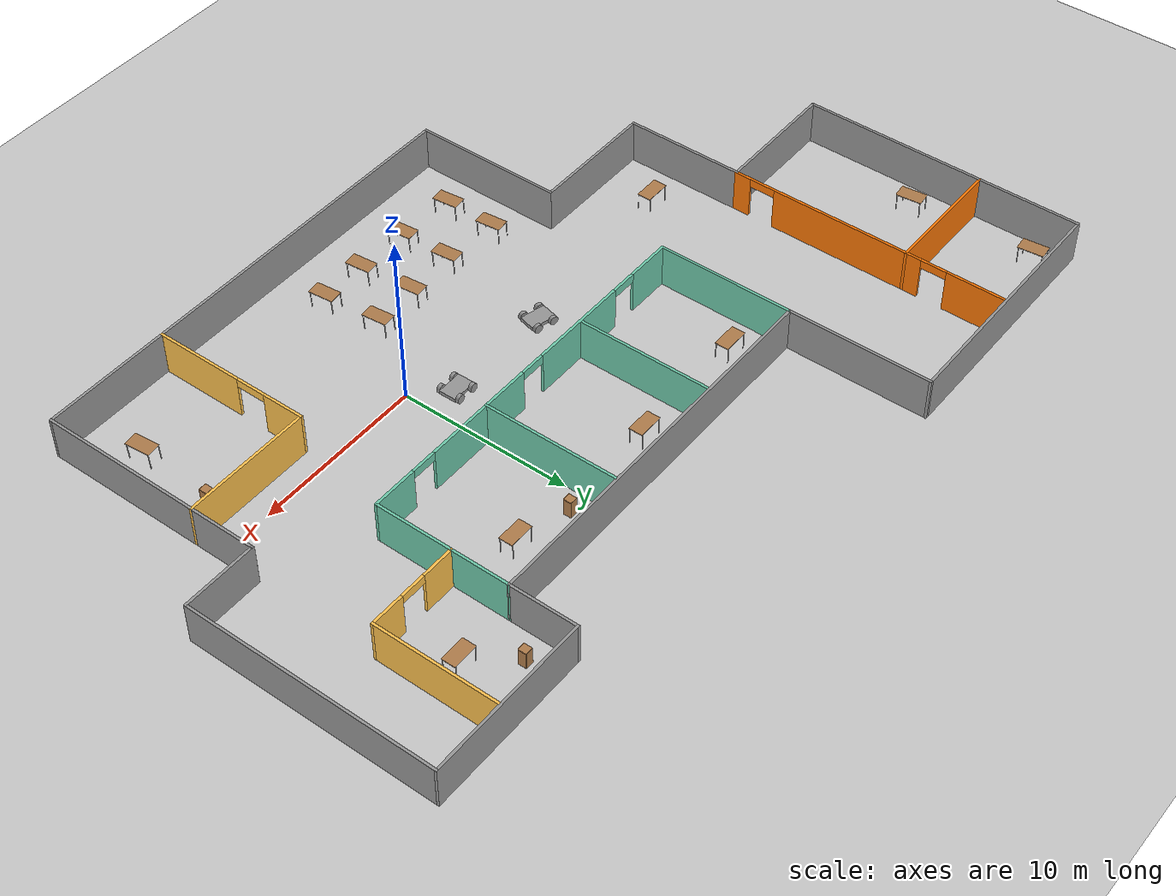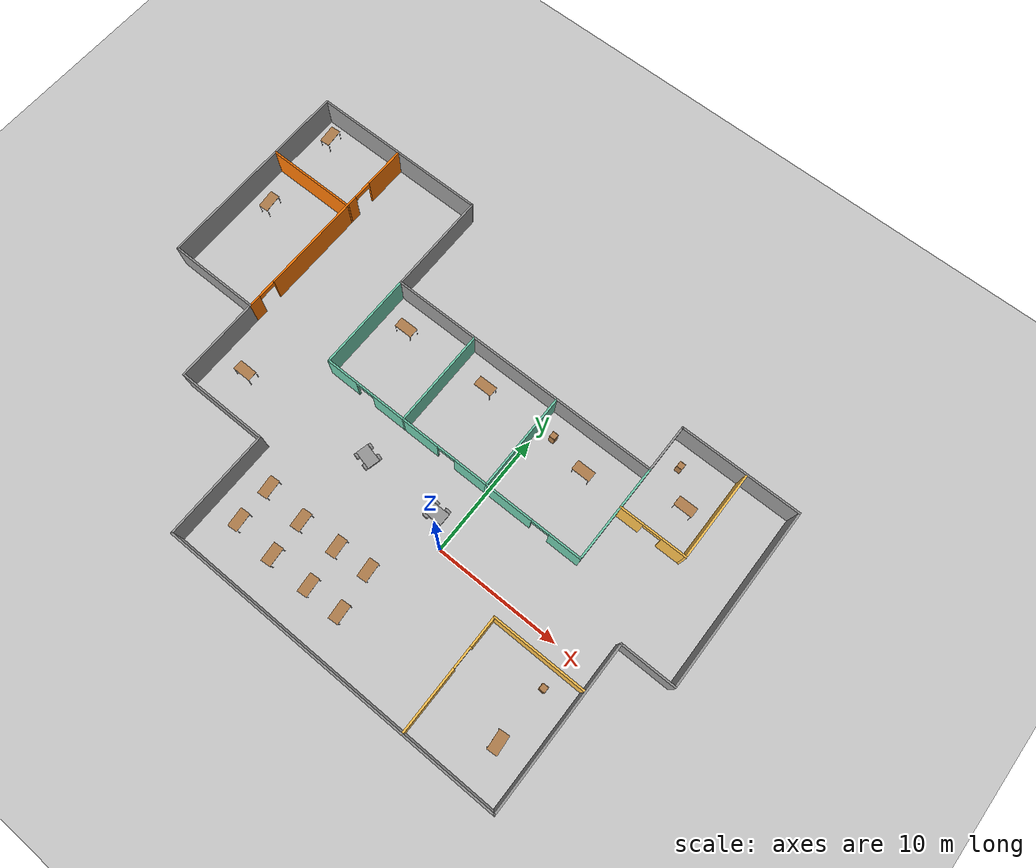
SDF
<sdf version="1.6">
 <world name="default">
  <plugin name="welcome_message" filename="libwelcome_message.so"/>
  <light name="sun" type="directional">
   <pose>0 0 10 0 -0 0</pose>
   <diffuse>0.8 0.8 0.8 1</diffuse>
   <specular>0.1 0.1 0.1 1</specular>
   <attenuation>
    <range>1000</range>
    <constant>0.9</constant>
    <linear>0.01</linear>
    <quadratic>0.001</quadratic>
   </attenuation>
   <direction>-0.5 0.5 -1</direction>
  </light>
  <model name="ground_plane">
   <static>1</static>
   <link name="link">
    <collision name="collision">
     <geometry><plane><normal>0 0 1</normal><size>100 100</size></plane></geometry>
     <surface><friction><ode><mu>100</mu><mu2>50</mu2></ode></friction></surface>
    </collision>
    <visual name="visual">
     <cast_shadows>0</cast_shadows>
     <geometry><plane><normal>0 0 1</normal><size>100 100</size></plane></geometry>
     <material>
      <script><uri>file://media/materials/scripts/gazebo.material</uri><name>Gazebo/Grey</name></script>
     </material>
    </visual>
   </link>
  </model>
  <gravity>0 0 -9.8</gravity>
  <magnetic_field>6e-06 2.3e-05 -4.2e-05</magnetic_field>
  <atmosphere type="adiabatic"/>
  <physics name="default_physics" default="0" type="ode">
   <max_step_size>0.001</max_step_size>
   <real_time_factor>1</real_time_factor>
   <real_time_update_rate>1000</real_time_update_rate>
  </physics>
  <scene><ambient>0.4 0.4 0.4 1</ambient><background>0.7 0.7 0.7 1</background><shadows>1</shadows></scene>
  <spherical_coordinates>
   <surface_model>EARTH_WGS84</surface_model>
   <latitude_deg>0</latitude_deg>
   <longitude_deg>0</longitude_deg>
   <elevation>0</elevation>
   <heading_deg>0</heading_deg>
  </spherical_coordinates>
  <model name="model">
   <pose>-5.7541 5.2784 0 0 -0 0</pose>
   <link name="Wall_10">
    <collision name="Wall_10_Collision">
     <geometry><box><size>16.6341 0.15 2.5</size></box></geometry>
     <pose>0 0 1.25 0 -0 0</pose>
    </collision>
    <visual name="Wall_10_Visual">
     <pose>0 0 1.25 0 -0 0</pose>
     <geometry><box><size>16.6341 0.15 2.5</size></box></geometry>
     <material>
      <script><uri>file://media/materials/scripts/gazebo.material</uri><name>Gazebo/Grey</name></script>
      <ambient>1 1 1 1</ambient>
     </material>
     <meta><layer>0</layer></meta>
    </visual>
    <pose>-23.275 7.725 0 0 0 -1.57079</pose>
   </link>
   <link name="Wall_11">
    <collision name="Wall_11_Collision">
     <geometry><box><size>7.5 0.15 2.5</size></box></geometry>
     <pose>0 0 1.25 0 -0 0</pose>
    </collision>
    <visual name="Wall_11_Visual">
     <pose>0 0 1.25 0 -0 0</pose>
     <geometry><box><size>7.5 0.15 2.5</size></box></geometry>
     <material>
      <script><uri>file://media/materials/scripts/gazebo.material</uri><name>Gazebo/Grey</name></script>
      <ambient>1 1 1 1</ambient>
     </material>
     <meta><layer>0</layer></meta>
    </visual>
    <pose>-19.6 -0.517 0 0 -0 1.5e-05</pose>
   </link>
   <link name="Wall_12">
    <collision name="Wall_12_Collision">
     <geometry><box><size>7 0.15 2.5</size></box></geometry>
     <pose>0 0 1.25 0 -0 0</pose>
    </collision>
    <visual name="Wall_12_Visual">
     <pose>0 0 1.25 0 -0 0</pose>
     <geometry><box><size>7 0.15 2.5</size></box></geometry>
     <material>
      <script><uri>file://media/materials/scripts/gazebo.material</uri><name>Gazebo/Grey</name></script>
      <ambient>1 1 1 1</ambient>
     </material>
     <meta><layer>0</layer></meta>
    </visual>
    <pose>-15.925 -3.942 0 0 0 -1.57077</pose>
   </link>
   <link name="Wall_13">
    <collision name="Wall_13_Collision">
     <geometry><box><size>7.5 0.15 2.5</size></box></geometry>
     <pose>0 0 1.25 0 -0 0</pose>
    </collision>
    <visual name="Wall_13_Visual">
     <pose>0 0 1.25 0 -0 0</pose>
     <geometry><box><size>7.5 0.15 2.5</size></box></geometry>
     <material>
      <script><uri>file://media/materials/scripts/gazebo.material</uri><name>Gazebo/Grey</name></script>
      <ambient>1 1 1 1</ambient>
     </material>
     <meta><layer>0</layer></meta>
    </visual>
    <pose>-12.2499 -7.36705 0 0 -0 0</pose>
   </link>
   <link name="Wall_14">
    <collision name="Wall_14_Collision">
     <geometry><box><size>8.75 0.15 2.5</size></box></geometry>
     <pose>0 0 1.25 0 -0 0</pose>
    </collision>
    <visual name="Wall_14_Visual">
     <pose>0 0 1.25 0 -0 0</pose>
     <geometry><box><size>8.75 0.15 2.5</size></box></geometry>
     <material>
      <script><uri>file://media/materials/scripts/gazebo.material</uri><name>Gazebo/Grey</name></script>
      <ambient>1 1 1 1</ambient>
     </material>
     <meta><layer>0</layer></meta>
    </visual>
    <pose>-8.57488 -11.6671 0 0 0 -1.5708</pose>
   </link>
   <link name="Wall_15">
    <collision name="Wall_15_Collision">
     <geometry><box><size>27.75 0.15 2.5</size></box></geometry>
     <pose>0 0 1.25 0 -0 0</pose>
    </collision>
    <visual name="Wall_15_Visual">
     <pose>0 0 1.25 0 -0 0</pose>
     <geometry><box><size>27.75 0.15 2.5</size></box></geometry>
     <material>
      <script><uri>file://media/materials/scripts/gazebo.material</uri><name>Gazebo/Grey</name></script>
      <ambient>1 1 1 1</ambient>
     </material>
     <meta><layer>0</layer></meta>
    </visual>
    <pose>5.22512 -15.9671 0 0 -0 0</pose>
   </link>
   <link name="Wall_17">
    <collision name="Wall_17_Collision">
     <geometry><box><size>13.25 0.15 2.5</size></box></geometry>
     <pose>0 0 1.25 0 -0 0</pose>
    </collision>
    <visual name="Wall_17_Visual">
     <pose>0 0 1.25 0 -0 0</pose>
     <geometry><box><size>13.25 0.15 2.5</size></box></geometry>
     <material>
      <script><uri>file://media/materials/scripts/gazebo.material</uri><name>Gazebo/Grey</name></script>
      <ambient>1 1 1 1</ambient>
     </material>
     <meta><layer>0</layer></meta>
    </visual>
    <pose>19.025 -9.417 0 0 -0 1.57081</pose>
   </link>
   <link name="Wall_18">
    <collision name="Wall_18_Collision">
     <geometry><box><size>4.4 0.15 2.5</size></box></geometry>
     <pose>0 0 1.25 0 -0 0</pose>
    </collision>
    <visual name="Wall_18_Visual">
     <pose>0 0 1.25 0 -0 0</pose>
     <geometry><box><size>4.4 0.15 2.5</size></box></geometry>
     <material>
      <script><uri>file://media/materials/scripts/gazebo.material</uri><name>Gazebo/Grey</name></script>
      <ambient>1 1 1 1</ambient>
     </material>
     <meta><layer>0</layer></meta>
    </visual>
    <pose>21.15 -2.86694 0 0 -0 0</pose>
   </link>
   <link name="Wall_20">
    <collision name="Wall_20_Collision">
     <geometry><box><size>8 0.15 2.5</size></box></geometry>
     <pose>0 0 1.25 0 -0 0</pose>
    </collision>
    <visual name="Wall_20_Visual">
     <pose>0 0 1.25 0 -0 0</pose>
     <geometry><box><size>8 0.15 2.5</size></box></geometry>
     <material>
      <script><uri>file://media/materials/scripts/gazebo.material</uri><name>Gazebo/Grey</name></script>
      <ambient>0.435294 0.796078 0.67451 1</ambient>
     </material>
     <meta><layer>0</layer></meta>
    </visual>
    <pose>-8.67504 3.79406 0 0 0 -1.5708</pose>
   </link>
   <link name="Wall_21">
    <pose>2.48846 -0.130945 0 0 -0 0</pose>
    <visual name="Wall_21_Visual_0">
     <pose>-9.88927 0 1.25 0 -0 0</pose>
     <geometry><box><size>2.69894 0.15 2.5</size></box></geometry>
     <material>
      <script><uri>file://media/materials/scripts/gazebo.material</uri><name>Gazebo/Grey</name></script>
      <ambient>0.435294 0.796078 0.67451 1</ambient>
     </material>
     <meta><layer>0</layer></meta>
    </visual>
    <collision name="Wall_21_Collision_0">
     <geometry><box><size>2.69894 0.15 2.5</size></box></geometry>
     <pose>-9.88927 0 1.25 0 -0 0</pose>
    </collision>
    <visual name="Wall_21_Visual_1">
     <pose>-4.08434 0 1.25 0 -0 0</pose>
     <geometry><box><size>5.91093 0.15 2.5</size></box></geometry>
     <material>
      <script><uri>file://media/materials/scripts/gazebo.material</uri><name>Gazebo/Grey</name></script>
      <ambient>0.435294 0.796078 0.67451 1</ambient>
     </material>
     <meta><layer>0</layer></meta>
    </visual>
    <collision name="Wall_21_Collision_1">
     <geometry><box><size>5.91093 0.15 2.5</size></box></geometry>
     <pose>-4.08434 0 1.25 0 -0 0</pose>
    </collision>
    <visual name="Wall_21_Visual_2">
     <pose>3.7245 0 1.25 0 -0 0</pose>
     <geometry><box><size>6.70674 0.15 2.5</size></box></geometry>
     <material>
      <script><uri>file://media/materials/scripts/gazebo.material</uri><name>Gazebo/Grey</name></script>
      <ambient>0.435294 0.796078 0.67451 1</ambient>
     </material>
     <meta><layer>0</layer></meta>
    </visual>
    <collision name="Wall_21_Collision_2">
     <geometry><box><size>6.70674 0.15 2.5</size></box></geometry>
     <pose>3.7245 0 1.25 0 -0 0</pose>
    </collision>
    <visual name="Wall_21_Visual_3">
     <pose>9.9083 0 1.25 0 -0 0</pose>
     <geometry><box><size>2.66088 0.15 2.5</size></box></geometry>
     <material>
      <script><uri>file://media/materials/scripts/gazebo.material</uri><name>Gazebo/Grey</name></script>
      <ambient>0.435294 0.796078 0.67451 1</ambient>
     </material>
     <meta><layer>0</layer></meta>
    </visual>
    <collision name="Wall_21_Collision_3">
     <geometry><box><size>2.66088 0.15 2.5</size></box></geometry>
     <pose>9.9083 0 1.25 0 -0 0</pose>
    </collision>
    <visual name="Wall_21_Visual_4">
     <pose>-7.7898 0 2.25 0 -0 0</pose>
     <geometry><box><size>1.5 0.15 0.5</size></box></geometry>
     <material>
      <script><uri>file://media/materials/scripts/gazebo.material</uri><name>Gazebo/Grey</name></script>
      <ambient>0.435294 0.796078 0.67451 1</ambient>
     </material>
     <meta><layer>0</layer></meta>
    </visual>
    <collision name="Wall_21_Collision_4">
     <geometry><box><size>1.5 0.15 0.5</size></box></geometry>
     <pose>-7.7898 0 2.25 0 -0 0</pose>
    </collision>
    <visual name="Wall_21_Visual_5">
     <pose>-0.378872 0 2.25 0 -0 0</pose>
     <geometry><box><size>1.5 0.15 0.5</size></box></geometry>
     <material>
      <script><uri>file://media/materials/scripts/gazebo.material</uri><name>Gazebo/Grey</name></script>
      <ambient>0.435294 0.796078 0.67451 1</ambient>
     </material>
     <meta><layer>0</layer></meta>
    </visual>
    <collision name="Wall_21_Collision_5">
     <geometry><box><size>1.5 0.15 0.5</size></box></geometry>
     <pose>-0.378872 0 2.25 0 -0 0</pose>
    </collision>
    <visual name="Wall_21_Visual_6">
     <pose>7.82787 0 2.25 0 -0 0</pose>
     <geometry><box><size>1.5 0.15 0.5</size></box></geometry>
     <material>
      <script><uri>file://media/materials/scripts/gazebo.material</uri><name>Gazebo/Grey</name></script>
      <ambient>0.435294 0.796078 0.67451 1</ambient>
     </material>
     <meta><layer>0</layer></meta>
    </visual>
    <collision name="Wall_21_Collision_6">
     <geometry><box><size>1.5 0.15 0.5</size></box></geometry>
     <pose>7.82787 0 2.25 0 -0 0</pose>
    </collision>
   </link>
   <link name="Wall_22">
    <collision name="Wall_22_Collision">
     <geometry><box><size>8.01356 0.15 2.5</size></box></geometry>
     <pose>0 0 1.25 0 -0 0</pose>
    </collision>
    <visual name="Wall_22_Visual">
     <pose>0 0 1.25 0 -0 0</pose>
     <geometry><box><size>8.01356 0.15 2.5</size></box></geometry>
     <material>
      <script><uri>file://media/materials/scripts/gazebo.material</uri><name>Gazebo/Grey</name></script>
      <ambient>0.435294 0.796078 0.67451 1</ambient>
     </material>
     <meta><layer>0</layer></meta>
    </visual>
    <pose>13.6635 3.80105 0 0 -0 1.56787</pose>
   </link>
   <link name="Wall_24">
    <collision name="Wall_24_Collision">
     <geometry><box><size>7.95 0.15 2.5</size></box></geometry>
     <pose>0 0 1.25 0 -0 0</pose>
    </collision>
    <visual name="Wall_24_Visual">
     <pose>0 0 1.25 0 -0 0</pose>
     <geometry><box><size>7.95 0.15 2.5</size></box></geometry>
     <material>
      <script><uri>file://media/materials/scripts/gazebo.material</uri><name>Gazebo/Grey</name></script>
      <ambient>0.435294 0.796078 0.67451 1</ambient>
     </material>
     <meta><layer>0</layer></meta>
    </visual>
    <pose>-1.75004 3.76905 0 0 0 -1.5708</pose>
   </link>
   <link name="Wall_26">
    <collision name="Wall_26_Collision">
     <geometry><box><size>7.945 0.15 2.5</size></box></geometry>
     <pose>0 0 1.25 0 -0 0</pose>
    </collision>
    <visual name="Wall_26_Visual">
     <pose>0 0 1.25 0 -0 0</pose>
     <geometry><box><size>7.945 0.15 2.5</size></box></geometry>
     <material>
      <script><uri>file://media/materials/scripts/gazebo.material</uri><name>Gazebo/Grey</name></script>
      <ambient>0.435294 0.796078 0.67451 1</ambient>
     </material>
     <meta><layer>0</layer></meta>
    </visual>
    <pose>5.64896 3.76655 0 0 0 -1.5708</pose>
   </link>
   <link name="Wall_28">
    <pose>-15.925 7.65806 0 0 -0 1.5708</pose>
    <visual name="Wall_28_Visual_0">
     <pose>-7.74683 0 1.25 0 -0 0</pose>
     <geometry><box><size>1.00633 0.15 2.5</size></box></geometry>
     <material>
      <script><uri>file://media/materials/scripts/gazebo.material</uri><name>Gazebo/Grey</name></script>
      <ambient>0.996078 0.47451 0.0196078 1</ambient>
     </material>
     <meta><layer>0</layer></meta>
    </visual>
    <collision name="Wall_28_Collision_0">
     <geometry><box><size>1.00633 0.15 2.5</size></box></geometry>
     <pose>-7.74683 0 1.25 0 -0 0</pose>
    </collision>
    <visual name="Wall_28_Visual_1">
     <pose>-1.21167 0 1.25 0 -0 0</pose>
     <geometry><box><size>9.06399 0.15 2.5</size></box></geometry>
     <material>
      <script><uri>file://media/materials/scripts/gazebo.material</uri><name>Gazebo/Grey</name></script>
      <ambient>0.996078 0.47451 0.0196078 1</ambient>
     </material>
     <meta><layer>0</layer></meta>
    </visual>
    <collision name="Wall_28_Collision_1">
     <geometry><box><size>9.06399 0.15 2.5</size></box></geometry>
     <pose>-1.21167 0 1.25 0 -0 0</pose>
    </collision>
    <visual name="Wall_28_Visual_2">
     <pose>6.53516 0 1.25 0 -0 0</pose>
     <geometry><box><size>3.42968 0.15 2.5</size></box></geometry>
     <material>
      <script><uri>file://media/materials/scripts/gazebo.material</uri><name>Gazebo/Grey</name></script>
      <ambient>0.996078 0.47451 0.0196078 1</ambient>
     </material>
     <meta><layer>0</layer></meta>
    </visual>
    <collision name="Wall_28_Collision_2">
     <geometry><box><size>3.42968 0.15 2.5</size></box></geometry>
     <pose>6.53516 0 1.25 0 -0 0</pose>
    </collision>
    <visual name="Wall_28_Visual_3">
     <pose>-6.49367 0 2.25 0 -0 0</pose>
     <geometry><box><size>1.5 0.15 0.5</size></box></geometry>
     <material>
      <script><uri>file://media/materials/scripts/gazebo.material</uri><name>Gazebo/Grey</name></script>
      <ambient>0.996078 0.47451 0.0196078 1</ambient>
     </material>
     <meta><layer>0</layer></meta>
    </visual>
    <collision name="Wall_28_Collision_3">
     <geometry><box><size>1.5 0.15 0.5</size></box></geometry>
     <pose>-6.49367 0 2.25 0 -0 0</pose>
    </collision>
    <visual name="Wall_28_Visual_4">
     <pose>4.07032 0 2.25 0 -0 0</pose>
     <geometry><box><size>1.5 0.15 0.5</size></box></geometry>
     <material>
      <script><uri>file://media/materials/scripts/gazebo.material</uri><name>Gazebo/Grey</name></script>
      <ambient>0.996078 0.47451 0.0196078 1</ambient>
     </material>
     <meta><layer>0</layer></meta>
    </visual>
    <collision name="Wall_28_Collision_4">
     <geometry><box><size>1.5 0.15 0.5</size></box></geometry>
     <pose>4.07032 0 2.25 0 -0 0</pose>
    </collision>
   </link>
   <link name="Wall_3">
    <collision name="Wall_3_Collision">
     <geometry><box><size>14.5999 0.15 2.5</size></box></geometry>
     <pose>0 0 1.25 0 -0 0</pose>
    </collision>
    <visual name="Wall_3_Visual">
     <pose>0 0 1.25 0 -0 0</pose>
     <geometry><box><size>14.5999 0.15 2.5</size></box></geometry>
     <material>
      <script><uri>file://media/materials/scripts/gazebo.material</uri><name>Gazebo/Grey</name></script>
      <ambient>1 1 1 1</ambient>
     </material>
     <meta><layer>0</layer></meta>
    </visual>
    <pose>23.275 4.35806 0 0 -0 1.5708</pose>
   </link>
   <link name="Wall_30">
    <collision name="Wall_30_Collision">
     <geometry><box><size>7.471 0.15 2.5</size></box></geometry>
     <pose>0 0 1.25 0 -0 0</pose>
    </collision>
    <visual name="Wall_30_Visual">
     <pose>0 0 1.25 0 -0 0</pose>
     <geometry><box><size>7.471 0.15 2.5</size></box></geometry>
     <material>
      <script><uri>file://media/materials/scripts/gazebo.material</uri><name>Gazebo/Grey</name></script>
      <ambient>0.996078 0.47451 0.0196078 1</ambient>
     </material>
     <meta><layer>0</layer></meta>
    </visual>
    <pose>-19.5855 10.0661 0 0 -0 0</pose>
   </link>
   <link name="Wall_32">
    <collision name="Wall_32_Collision">
     <geometry><box><size>7.25 0.15 2.5</size></box></geometry>
     <pose>0 0 1.25 0 -0 0</pose>
    </collision>
    <visual name="Wall_32_Visual">
     <pose>0 0 1.25 0 -0 0</pose>
     <geometry><box><size>7.25 0.15 2.5</size></box></geometry>
     <material>
      <script><uri>file://media/materials/scripts/gazebo.material</uri><name>Gazebo/Grey</name></script>
      <ambient>1 0.764706 0.305882 1</ambient>
     </material>
     <meta><layer>0</layer></meta>
    </visual>
    <pose>19.033 7.91005 0 0 0 -1.5708</pose>
   </link>
   <link name="Wall_33">
    <pose>16.358 4.36006 0 0 -0 3.14159</pose>
    <visual name="Wall_33_Visual_0">
     <pose>-1.73876 0 1.25 0 -0 0</pose>
     <geometry><box><size>2.02248 0.15 2.5</size></box></geometry>
     <material>
      <script><uri>file://media/materials/scripts/gazebo.material</uri><name>Gazebo/Grey</name></script>
      <ambient>1 0.764706 0.305882 1</ambient>
     </material>
     <meta><layer>0</layer></meta>
    </visual>
    <collision name="Wall_33_Collision_0">
     <geometry><box><size>2.02248 0.15 2.5</size></box></geometry>
     <pose>-1.73876 0 1.25 0 -0 0</pose>
    </collision>
    <visual name="Wall_33_Visual_1">
     <pose>1.76124 0 1.25 0 -0 0</pose>
     <geometry><box><size>1.97752 0.15 2.5</size></box></geometry>
     <material>
      <script><uri>file://media/materials/scripts/gazebo.material</uri><name>Gazebo/Grey</name></script>
      <ambient>1 0.764706 0.305882 1</ambient>
     </material>
     <meta><layer>0</layer></meta>
    </visual>
    <collision name="Wall_33_Collision_1">
     <geometry><box><size>1.97752 0.15 2.5</size></box></geometry>
     <pose>1.76124 0 1.25 0 -0 0</pose>
    </collision>
    <visual name="Wall_33_Visual_2">
     <pose>0.022481 0 2.25 0 -0 0</pose>
     <geometry><box><size>1.5 0.15 0.5</size></box></geometry>
     <material>
      <script><uri>file://media/materials/scripts/gazebo.material</uri><name>Gazebo/Grey</name></script>
      <ambient>1 0.764706 0.305882 1</ambient>
     </material>
     <meta><layer>0</layer></meta>
    </visual>
    <collision name="Wall_33_Collision_2">
     <geometry><box><size>1.5 0.15 0.5</size></box></geometry>
     <pose>0.022481 0 2.25 0 -0 0</pose>
    </collision>
   </link>
   <link name="Wall_36">
    <collision name="Wall_36_Collision">
     <geometry><box><size>7.572 0.15 2.5</size></box></geometry>
     <pose>0 0 1.25 0 -0 0</pose>
    </collision>
    <visual name="Wall_36_Visual">
     <pose>0 0 1.25 0 -0 0</pose>
     <geometry><box><size>7.572 0.15 2.5</size></box></geometry>
     <material>
      <script><uri>file://media/materials/scripts/gazebo.material</uri><name>Gazebo/Grey</name></script>
      <ambient>1 0.764706 0.305882 1</ambient>
     </material>
     <meta><layer>0</layer></meta>
    </visual>
    <pose>15.314 -6.68694 0 0 -0 0</pose>
   </link>
   <link name="Wall_38">
    <pose>11.603 -11.3269 0 0 0 -1.5708</pose>
    <visual name="Wall_38_Visual_0">
     <pose>-3.47456 0 1.25 0 -0 0</pose>
     <geometry><box><size>2.48088 0.15 2.5</size></box></geometry>
     <material>
      <script><uri>file://media/materials/scripts/gazebo.material</uri><name>Gazebo/Grey</name></script>
      <ambient>1 0.764706 0.305882 1</ambient>
     </material>
     <meta><layer>0</layer></meta>
    </visual>
    <collision name="Wall_38_Collision_0">
     <geometry><box><size>2.48088 0.15 2.5</size></box></geometry>
     <pose>-3.47456 0 1.25 0 -0 0</pose>
    </collision>
    <visual name="Wall_38_Visual_1">
     <pose>2.11544 0 1.25 0 -0 0</pose>
     <geometry><box><size>5.19912 0.15 2.5</size></box></geometry>
     <material>
      <script><uri>file://media/materials/scripts/gazebo.material</uri><name>Gazebo/Grey</name></script>
      <ambient>1 0.764706 0.305882 1</ambient>
     </material>
     <meta><layer>0</layer></meta>
    </visual>
    <collision name="Wall_38_Collision_1">
     <geometry><box><size>5.19912 0.15 2.5</size></box></geometry>
     <pose>2.11544 0 1.25 0 -0 0</pose>
    </collision>
    <visual name="Wall_38_Visual_2">
     <pose>-1.35912 0 2.25 0 -0 0</pose>
     <geometry><box><size>1.75 0.15 0.5</size></box></geometry>
     <material>
      <script><uri>file://media/materials/scripts/gazebo.material</uri><name>Gazebo/Grey</name></script>
      <ambient>1 0.764706 0.305882 1</ambient>
     </material>
     <meta><layer>0</layer></meta>
    </visual>
    <collision name="Wall_38_Collision_2">
     <geometry><box><size>1.75 0.15 0.5</size></box></geometry>
     <pose>-1.35912 0 2.25 0 -0 0</pose>
    </collision>
   </link>
   <link name="Wall_5">
    <collision name="Wall_5_Collision">
     <geometry><box><size>9.75 0.15 2.5</size></box></geometry>
     <pose>0 0 1.25 0 -0 0</pose>
    </collision>
    <visual name="Wall_5_Visual">
     <pose>0 0 1.25 0 -0 0</pose>
     <geometry><box><size>9.75 0.15 2.5</size></box></geometry>
     <material>
      <script><uri>file://media/materials/scripts/gazebo.material</uri><name>Gazebo/Grey</name></script>
      <ambient>1 1 1 1</ambient>
     </material>
     <meta><layer>0</layer></meta>
    </visual>
    <pose>18.475 11.583 0 0 0 -3.14158</pose>
   </link>
   <link name="Wall_6">
    <collision name="Wall_6_Collision">
     <geometry><box><size>4 0.15 2.5</size></box></geometry>
     <pose>0 0 1.25 0 -0 0</pose>
    </collision>
    <visual name="Wall_6_Visual">
     <pose>0 0 1.25 0 -0 0</pose>
     <geometry><box><size>4 0.15 2.5</size></box></geometry>
     <material>
      <script><uri>file://media/materials/scripts/gazebo.material</uri><name>Gazebo/Grey</name></script>
      <ambient>1 1 1 1</ambient>
     </material>
     <meta><layer>0</layer></meta>
    </visual>
    <pose>13.675 9.658 0 0 0 -1.57084</pose>
   </link>
   <link name="Wall_7">
    <collision name="Wall_7_Collision">
     <geometry><box><size>22.5 0.15 2.5</size></box></geometry>
     <pose>0 0 1.25 0 -0 0</pose>
    </collision>
    <visual name="Wall_7_Visual">
     <pose>0 0 1.25 0 -0 0</pose>
     <geometry><box><size>22.5 0.15 2.5</size></box></geometry>
     <material>
      <script><uri>file://media/materials/scripts/gazebo.material</uri><name>Gazebo/Grey</name></script>
      <ambient>1 1 1 1</ambient>
     </material>
     <meta><layer>0</layer></meta>
    </visual>
    <pose>2.49996 7.73306 0 0 -0 3.14159</pose>
   </link>
   <link name="Wall_8">
    <collision name="Wall_8_Collision">
     <geometry><box><size>8.384 0.15 2.5</size></box></geometry>
     <pose>0 0 1.25 0 -0 0</pose>
    </collision>
    <visual name="Wall_8_Visual">
     <pose>0 0 1.25 0 -0 0</pose>
     <geometry><box><size>8.384 0.15 2.5</size></box></geometry>
     <material>
      <script><uri>file://media/materials/scripts/gazebo.material</uri><name>Gazebo/Grey</name></script>
      <ambient>1 1 1 1</ambient>
     </material>
     <meta><layer>0</layer></meta>
    </visual>
    <pose>-8.67504 11.8501 0 0 -0 1.5708</pose>
   </link>
   <link name="Wall_9">
    <collision name="Wall_9_Collision">
     <geometry><box><size>14.75 0.15 2.5</size></box></geometry>
     <pose>0 0 1.25 0 -0 0</pose>
    </collision>
    <visual name="Wall_9_Visual">
     <pose>0 0 1.25 0 -0 0</pose>
     <geometry><box><size>14.75 0.15 2.5</size></box></geometry>
     <material>
      <script><uri>file://media/materials/scripts/gazebo.material</uri><name>Gazebo/Grey</name></script>
      <ambient>1 1 1 1</ambient>
     </material>
     <meta><layer>0</layer></meta>
    </visual>
    <pose>-15.975 15.9671 0 0 -0 3.14159</pose>
   </link>
   <static>1</static>
  </model>
  <model name="model_0">
   <link name="link_0">
    <pose>0 0 -0.016 0 -0 0</pose>
    <inertial>
     <mass>1</mass>
     <inertia>
      <ixx>0.166667</ixx>
      <ixy>0</ixy>
      <ixz>0</ixz>
      <iyy>0.166667</iyy>
      <iyz>0</iyz>
      <izz>0.166667</izz>
     </inertia>
    </inertial>
    <visual name="visual">
     <geometry><box><size>1.5 1 0.2</size></box></geometry>
     <material>
      <lighting>1</lighting>
      <script><uri>file://media/materials/scripts/gazebo.material</uri><name>Gazebo/Grey</name></script>
      <shader type="pixel"><normal_map>__default__</normal_map></shader>
      <ambient>0.3 0.3 0.3 1</ambient>
      <diffuse>0.7 0.7 0.7 1</diffuse>
      <specular>0.01 0.01 0.01 1</specular>
      <emissive>0 0 0 1</emissive>
     </material>
    </visual>
    <collision name="collision">
     <geometry><box><size>1.5 1 0.2</size></box></geometry>
     <surface>
      <friction>
       <ode><mu>1</mu><mu2>1</mu2><fdir1>0 0 0</fdir1><slip1>0</slip1><slip2>0</slip2></ode>
       <torsional>
        <coefficient>1</coefficient>
        <patch_radius>0</patch_radius>
        <surface_radius>0</surface_radius>
        <use_patch_radius>1</use_patch_radius>
        <ode><slip>0</slip></ode>
       </torsional>
      </friction>
      <bounce><restitution_coefficient>0</restitution_coefficient><threshold>1e+06</threshold></bounce>
      <contact>
       <collide_without_contact>0</collide_without_contact>
       <collide_without_contact_bitmask>1</collide_without_contact_bitmask>
       <collide_bitmask>1</collide_bitmask>
       <ode>
        <soft_cfm>0</soft_cfm>
        <soft_erp>0.2</soft_erp>
        <kp>1e+13</kp>
        <kd>1</kd>
        <max_vel>0.01</max_vel>
        <min_depth>0</min_depth>
       </ode>
       <bullet>
        <split_impulse>1</split_impulse>
        <split_impulse_penetration_threshold>-0.01</split_impulse_penetration_threshold>
        <soft_cfm>0</soft_cfm>
        <soft_erp>0.2</soft_erp>
        <kp>1e+13</kp>
        <kd>1</kd>
       </bullet>
      </contact>
     </surface>
    </collision>
   </link>
   <link name="link_1">
    <pose>0.5 -0.6 0.004 -1.57079 0 0</pose>
    <inertial>
     <mass>1</mass>
     <inertia><ixx>0.145833</ixx><ixy>0</ixy><ixz>0</ixz><iyy>0.145833</iyy><iyz>0</iyz><izz>0.125</izz></inertia>
    </inertial>
    <visual name="visual">
     <geometry><cylinder><radius>0.25</radius><length>0.2</length></cylinder></geometry>
     <material>
      <lighting>1</lighting>
      <script><uri>file://media/materials/scripts/gazebo.material</uri><name>Gazebo/Grey</name></script>
      <shader type="pixel"><normal_map>__default__</normal_map></shader>
      <ambient>0.3 0.3 0.3 1</ambient>
      <diffuse>0.7 0.7 0.7 1</diffuse>
      <specular>0.01 0.01 0.01 1</specular>
      <emissive>0 0 0 1</emissive>
     </material>
    </visual>
    <collision name="collision">
     <geometry><cylinder><radius>0.25</radius><length>0.2</length></cylinder></geometry>
     <surface>
      <friction>
       <ode><mu>1</mu><mu2>1</mu2><fdir1>0 0 0</fdir1><slip1>0</slip1><slip2>0</slip2></ode>
       <torsional>
        <coefficient>1</coefficient>
        <patch_radius>0</patch_radius>
        <surface_radius>0</surface_radius>
        <use_patch_radius>1</use_patch_radius>
        <ode><slip>0</slip></ode>
       </torsional>
      </friction>
      <bounce><restitution_coefficient>0</restitution_coefficient><threshold>1e+06</threshold></bounce>
      <contact>
       <collide_without_contact>0</collide_without_contact>
       <collide_without_contact_bitmask>1</collide_without_contact_bitmask>
       <collide_bitmask>1</collide_bitmask>
       <ode>
        <soft_cfm>0</soft_cfm>
        <soft_erp>0.2</soft_erp>
        <kp>1e+13</kp>
        <kd>1</kd>
        <max_vel>0.01</max_vel>
        <min_depth>0</min_depth>
       </ode>
       <bullet>
        <split_impulse>1</split_impulse>
        <split_impulse_penetration_threshold>-0.01</split_impulse_penetration_threshold>
        <soft_cfm>0</soft_cfm>
        <soft_erp>0.2</soft_erp>
        <kp>1e+13</kp>
        <kd>1</kd>
       </bullet>
      </contact>
     </surface>
    </collision>
   </link>
   <link name="link_1_clone">
    <pose>0.5 0.6 0.004 1.57079 -0 0</pose>
    <inertial>
     <mass>1</mass>
     <inertia><ixx>0.145833</ixx><ixy>0</ixy><ixz>0</ixz><iyy>0.145833</iyy><iyz>0</iyz><izz>0.125</izz></inertia>
    </inertial>
    <visual name="visual">
     <geometry><cylinder><radius>0.25</radius><length>0.2</length></cylinder></geometry>
     <material>
      <lighting>1</lighting>
      <script><uri>file://media/materials/scripts/gazebo.material</uri><name>Gazebo/Grey</name></script>
      <shader type="pixel"><normal_map>__default__</normal_map></shader>
      <ambient>0.3 0.3 0.3 1</ambient>
      <diffuse>0.7 0.7 0.7 1</diffuse>
      <specular>0.01 0.01 0.01 1</specular>
      <emissive>0 0 0 1</emissive>
     </material>
    </visual>
    <collision name="collision">
     <geometry><cylinder><radius>0.25</radius><length>0.2</length></cylinder></geometry>
     <surface>
      <friction>
       <ode><mu>1</mu><mu2>1</mu2><fdir1>0 0 0</fdir1><slip1>0</slip1><slip2>0</slip2></ode>
       <torsional>
        <coefficient>1</coefficient>
        <patch_radius>0</patch_radius>
        <surface_radius>0</surface_radius>
        <use_patch_radius>1</use_patch_radius>
        <ode><slip>0</slip></ode>
       </torsional>
      </friction>
      <bounce><restitution_coefficient>0</restitution_coefficient><threshold>1e+06</threshold></bounce>
      <contact>
       <collide_without_contact>0</collide_without_contact>
       <collide_without_contact_bitmask>1</collide_without_contact_bitmask>
       <collide_bitmask>1</collide_bitmask>
       <ode>
        <soft_cfm>0</soft_cfm>
        <soft_erp>0.2</soft_erp>
        <kp>1e+13</kp>
        <kd>1</kd>
        <max_vel>0.01</max_vel>
        <min_depth>0</min_depth>
       </ode>
       <bullet>
        <split_impulse>1</split_impulse>
        <split_impulse_penetration_threshold>-0.01</split_impulse_penetration_threshold>
        <soft_cfm>0</soft_cfm>
        <soft_erp>0.2</soft_erp>
        <kp>1e+13</kp>
        <kd>1</kd>
       </bullet>
      </contact>
     </surface>
    </collision>
   </link>
   <link name="link_1_clone_0">
    <pose>-0.5 0.6 0.004 1.57079 -0 0</pose>
    <inertial>
     <mass>1</mass>
     <inertia><ixx>0.145833</ixx><ixy>0</ixy><ixz>0</ixz><iyy>0.145833</iyy><iyz>0</iyz><izz>0.125</izz></inertia>
    </inertial>
    <visual name="visual">
     <geometry><cylinder><radius>0.25</radius><length>0.2</length></cylinder></geometry>
     <material>
      <lighting>1</lighting>
      <script><uri>file://media/materials/scripts/gazebo.material</uri><name>Gazebo/Grey</name></script>
      <shader type="pixel"><normal_map>__default__</normal_map></shader>
      <ambient>0.3 0.3 0.3 1</ambient>
      <diffuse>0.7 0.7 0.7 1</diffuse>
      <specular>0.01 0.01 0.01 1</specular>
      <emissive>0 0 0 1</emissive>
     </material>
    </visual>
    <collision name="collision">
     <geometry><cylinder><radius>0.25</radius><length>0.2</length></cylinder></geometry>
     <surface>
      <friction>
       <ode><mu>1</mu><mu2>1</mu2><fdir1>0 0 0</fdir1><slip1>0</slip1><slip2>0</slip2></ode>
       <torsional>
        <coefficient>1</coefficient>
        <patch_radius>0</patch_radius>
        <surface_radius>0</surface_radius>
        <use_patch_radius>1</use_patch_radius>
        <ode><slip>0</slip></ode>
       </torsional>
      </friction>
      <bounce><restitution_coefficient>0</restitution_coefficient><threshold>1e+06</threshold></bounce>
      <contact>
       <collide_without_contact>0</collide_without_contact>
       <collide_without_contact_bitmask>1</collide_without_contact_bitmask>
       <collide_bitmask>1</collide_bitmask>
       <ode>
        <soft_cfm>0</soft_cfm>
        <soft_erp>0.2</soft_erp>
        <kp>1e+13</kp>
        <kd>1</kd>
        <max_vel>0.01</max_vel>
        <min_depth>0</min_depth>
       </ode>
       <bullet>
        <split_impulse>1</split_impulse>
        <split_impulse_penetration_threshold>-0.01</split_impulse_penetration_threshold>
        <soft_cfm>0</soft_cfm>
        <soft_erp>0.2</soft_erp>
        <kp>1e+13</kp>
        <kd>1</kd>
       </bullet>
      </contact>
     </surface>
    </collision>
   </link>
   <link name="link_1_clone_1">
    <pose>-0.5 -0.6 0.004 -1.57079 0 0</pose>
    <inertial>
     <mass>1</mass>
     <inertia><ixx>0.145833</ixx><ixy>0</ixy><ixz>0</ixz><iyy>0.145833</iyy><iyz>0</iyz><izz>0.125</izz></inertia>
    </inertial>
    <visual name="visual">
     <geometry><cylinder><radius>0.25</radius><length>0.2</length></cylinder></geometry>
     <material>
      <lighting>1</lighting>
      <script><uri>file://media/materials/scripts/gazebo.material</uri><name>Gazebo/Grey</name></script>
      <shader type="pixel"><normal_map>__default__</normal_map></shader>
      <ambient>0.3 0.3 0.3 1</ambient>
      <diffuse>0.7 0.7 0.7 1</diffuse>
      <specular>0.01 0.01 0.01 1</specular>
      <emissive>0 0 0 1</emissive>
     </material>
    </visual>
    <collision name="collision">
     <geometry><cylinder><radius>0.25</radius><length>0.2</length></cylinder></geometry>
     <surface>
      <friction>
       <ode><mu>1</mu><mu2>1</mu2><fdir1>0 0 0</fdir1><slip1>0</slip1><slip2>0</slip2></ode>
       <torsional>
        <coefficient>1</coefficient>
        <patch_radius>0</patch_radius>
        <surface_radius>0</surface_radius>
        <use_patch_radius>1</use_patch_radius>
        <ode><slip>0</slip></ode>
       </torsional>
      </friction>
      <bounce><restitution_coefficient>0</restitution_coefficient><threshold>1e+06</threshold></bounce>
      <contact>
       <collide_without_contact>0</collide_without_contact>
       <collide_without_contact_bitmask>1</collide_without_contact_bitmask>
       <collide_bitmask>1</collide_bitmask>
       <ode>
        <soft_cfm>0</soft_cfm>
        <soft_erp>0.2</soft_erp>
        <kp>1e+13</kp>
        <kd>1</kd>
        <max_vel>0.01</max_vel>
        <min_depth>0</min_depth>
       </ode>
       <bullet>
        <split_impulse>1</split_impulse>
        <split_impulse_penetration_threshold>-0.01</split_impulse_penetration_threshold>
        <soft_cfm>0</soft_cfm>
        <soft_erp>0.2</soft_erp>
        <kp>1e+13</kp>
        <kd>1</kd>
       </bullet>
      </contact>
     </surface>
    </collision>
   </link>
   <joint name="link_0_JOINT_1" type="revolute">
    <parent>link_0</parent>
    <child>link_1_clone</child>
    <axis>
     <xyz>0 0 1</xyz>
     <use_parent_model_frame>0</use_parent_model_frame>
     <limit>
      <lower>-1.79769e+308</lower>
      <upper>1.79769e+308</upper>
      <effort>-1</effort>
      <velocity>-1</velocity>
     </limit>
     <dynamics>
      <spring_reference>0</spring_reference>
      <spring_stiffness>0</spring_stiffness>
      <damping>0</damping>
     </dynamics>
    </axis>
    <physics>
     <ode><limit><cfm>0</cfm><erp>0.2</erp></limit><suspension><cfm>0</cfm><erp>0.2</erp></suspension></ode>
    </physics>
   </joint>
   <joint name="link_0_JOINT_2" type="revolute">
    <parent>link_0</parent>
    <child>link_1</child>
    <axis>
     <xyz>0 0 1</xyz>
     <use_parent_model_frame>0</use_parent_model_frame>
     <limit>
      <lower>-1.79769e+308</lower>
      <upper>1.79769e+308</upper>
      <effort>-1</effort>
      <velocity>-1</velocity>
     </limit>
     <dynamics>
      <spring_reference>0</spring_reference>
      <spring_stiffness>0</spring_stiffness>
      <damping>0</damping>
     </dynamics>
    </axis>
    <physics>
     <ode><limit><cfm>0</cfm><erp>0.2</erp></limit><suspension><cfm>0</cfm><erp>0.2</erp></suspension></ode>
    </physics>
   </joint>
   <joint name="link_0_JOINT_3" type="revolute">
    <parent>link_0</parent>
    <child>link_1_clone_0</child>
    <axis>
     <xyz>0 0 1</xyz>
     <use_parent_model_frame>0</use_parent_model_frame>
     <limit>
      <lower>-1.79769e+308</lower>
      <upper>1.79769e+308</upper>
      <effort>-1</effort>
      <velocity>-1</velocity>
     </limit>
     <dynamics>
      <spring_reference>0</spring_reference>
      <spring_stiffness>0</spring_stiffness>
      <damping>0</damping>
     </dynamics>
    </axis>
    <physics>
     <ode><limit><cfm>0</cfm><erp>0.2</erp></limit><suspension><cfm>0</cfm><erp>0.2</erp></suspension></ode>
    </physics>
   </joint>
   <joint name="link_0_JOINT_4" type="revolute">
    <parent>link_0</parent>
    <child>link_1_clone_1</child>
    <axis>
     <xyz>0 0 1</xyz>
     <use_parent_model_frame>0</use_parent_model_frame>
     <limit>
      <lower>-1.79769e+308</lower>
      <upper>1.79769e+308</upper>
      <effort>-1</effort>
      <velocity>-1</velocity>
     </limit>
     <dynamics>
      <spring_reference>0</spring_reference>
      <spring_stiffness>0</spring_stiffness>
      <damping>0</damping>
     </dynamics>
    </axis>
    <physics>
     <ode><limit><cfm>0</cfm><erp>0.2</erp></limit><suspension><cfm>0</cfm><erp>0.2</erp></suspension></ode>
    </physics>
   </joint>
   <static>0</static>
   <pose>-8.21437 1.85942 0.246001 0 0 -0.24031</pose>
  </model>
  <model name="model_1">
   <link name="link_0">
    <pose>0 0 -0.016 0 -0 0</pose>
    <inertial>
     <mass>1</mass>
     <inertia>
      <ixx>0.166667</ixx>
      <ixy>0</ixy>
      <ixz>0</ixz>
      <iyy>0.166667</iyy>
      <iyz>0</iyz>
      <izz>0.166667</izz>
     </inertia>
    </inertial>
    <visual name="visual">
     <geometry><box><size>1.5 1 0.2</size></box></geometry>
     <material>
      <lighting>1</lighting>
      <script><uri>file://media/materials/scripts/gazebo.material</uri><name>Gazebo/Grey</name></script>
      <shader type="pixel"><normal_map>__default__</normal_map></shader>
      <ambient>0.3 0.3 0.3 1</ambient>
      <diffuse>0.7 0.7 0.7 1</diffuse>
      <specular>0.01 0.01 0.01 1</specular>
      <emissive>0 0 0 1</emissive>
     </material>
    </visual>
    <collision name="collision">
     <geometry><box><size>1.5 1 0.2</size></box></geometry>
     <surface>
      <friction>
       <ode><mu>1</mu><mu2>1</mu2><fdir1>0 0 0</fdir1><slip1>0</slip1><slip2>0</slip2></ode>
       <torsional>
        <coefficient>1</coefficient>
        <patch_radius>0</patch_radius>
        <surface_radius>0</surface_radius>
        <use_patch_radius>1</use_patch_radius>
        <ode><slip>0</slip></ode>
       </torsional>
      </friction>
      <bounce><restitution_coefficient>0</restitution_coefficient><threshold>1e+06</threshold></bounce>
      <contact>
       <collide_without_contact>0</collide_without_contact>
       <collide_without_contact_bitmask>1</collide_without_contact_bitmask>
       <collide_bitmask>1</collide_bitmask>
       <ode>
        <soft_cfm>0</soft_cfm>
        <soft_erp>0.2</soft_erp>
        <kp>1e+13</kp>
        <kd>1</kd>
        <max_vel>0.01</max_vel>
        <min_depth>0</min_depth>
       </ode>
       <bullet>
        <split_impulse>1</split_impulse>
        <split_impulse_penetration_threshold>-0.01</split_impulse_penetration_threshold>
        <soft_cfm>0</soft_cfm>
        <soft_erp>0.2</soft_erp>
        <kp>1e+13</kp>
        <kd>1</kd>
       </bullet>
      </contact>
     </surface>
    </collision>
   </link>
   <link name="link_1">
    <pose>0.5 -0.6 0.004 -1.57079 0 0</pose>
    <inertial>
     <mass>1</mass>
     <inertia><ixx>0.145833</ixx><ixy>0</ixy><ixz>0</ixz><iyy>0.145833</iyy><iyz>0</iyz><izz>0.125</izz></inertia>
    </inertial>
    <visual name="visual">
     <geometry><cylinder><radius>0.25</radius><length>0.2</length></cylinder></geometry>
     <material>
      <lighting>1</lighting>
      <script><uri>file://media/materials/scripts/gazebo.material</uri><name>Gazebo/Grey</name></script>
      <shader type="pixel"><normal_map>__default__</normal_map></shader>
      <ambient>0.3 0.3 0.3 1</ambient>
      <diffuse>0.7 0.7 0.7 1</diffuse>
      <specular>0.01 0.01 0.01 1</specular>
      <emissive>0 0 0 1</emissive>
     </material>
    </visual>
    <collision name="collision">
     <geometry><cylinder><radius>0.25</radius><length>0.2</length></cylinder></geometry>
     <surface>
      <friction>
       <ode><mu>1</mu><mu2>1</mu2><fdir1>0 0 0</fdir1><slip1>0</slip1><slip2>0</slip2></ode>
       <torsional>
        <coefficient>1</coefficient>
        <patch_radius>0</patch_radius>
        <surface_radius>0</surface_radius>
        <use_patch_radius>1</use_patch_radius>
        <ode><slip>0</slip></ode>
       </torsional>
      </friction>
      <bounce><restitution_coefficient>0</restitution_coefficient><threshold>1e+06</threshold></bounce>
      <contact>
       <collide_without_contact>0</collide_without_contact>
       <collide_without_contact_bitmask>1</collide_without_contact_bitmask>
       <collide_bitmask>1</collide_bitmask>
       <ode>
        <soft_cfm>0</soft_cfm>
        <soft_erp>0.2</soft_erp>
        <kp>1e+13</kp>
        <kd>1</kd>
        <max_vel>0.01</max_vel>
        <min_depth>0</min_depth>
       </ode>
       <bullet>
        <split_impulse>1</split_impulse>
        <split_impulse_penetration_threshold>-0.01</split_impulse_penetration_threshold>
        <soft_cfm>0</soft_cfm>
        <soft_erp>0.2</soft_erp>
        <kp>1e+13</kp>
        <kd>1</kd>
       </bullet>
      </contact>
     </surface>
    </collision>
   </link>
   <link name="link_1_clone">
    <pose>0.5 0.6 0.004 1.57079 -0 0</pose>
    <inertial>
     <mass>1</mass>
     <inertia><ixx>0.145833</ixx><ixy>0</ixy><ixz>0</ixz><iyy>0.145833</iyy><iyz>0</iyz><izz>0.125</izz></inertia>
    </inertial>
    <visual name="visual">
     <geometry><cylinder><radius>0.25</radius><length>0.2</length></cylinder></geometry>
     <material>
      <lighting>1</lighting>
      <script><uri>file://media/materials/scripts/gazebo.material</uri><name>Gazebo/Grey</name></script>
      <shader type="pixel"><normal_map>__default__</normal_map></shader>
      <ambient>0.3 0.3 0.3 1</ambient>
      <diffuse>0.7 0.7 0.7 1</diffuse>
      <specular>0.01 0.01 0.01 1</specular>
      <emissive>0 0 0 1</emissive>
     </material>
    </visual>
    <collision name="collision">
     <geometry><cylinder><radius>0.25</radius><length>0.2</length></cylinder></geometry>
     <surface>
      <friction>
       <ode><mu>1</mu><mu2>1</mu2><fdir1>0 0 0</fdir1><slip1>0</slip1><slip2>0</slip2></ode>
       <torsional>
        <coefficient>1</coefficient>
        <patch_radius>0</patch_radius>
        <surface_radius>0</surface_radius>
        <use_patch_radius>1</use_patch_radius>
        <ode><slip>0</slip></ode>
       </torsional>
      </friction>
      <bounce><restitution_coefficient>0</restitution_coefficient><threshold>1e+06</threshold></bounce>
      <contact>
       <collide_without_contact>0</collide_without_contact>
       <collide_without_contact_bitmask>1</collide_without_contact_bitmask>
       <collide_bitmask>1</collide_bitmask>
       <ode>
        <soft_cfm>0</soft_cfm>
        <soft_erp>0.2</soft_erp>
        <kp>1e+13</kp>
        <kd>1</kd>
        <max_vel>0.01</max_vel>
        <min_depth>0</min_depth>
       </ode>
       <bullet>
        <split_impulse>1</split_impulse>
        <split_impulse_penetration_threshold>-0.01</split_impulse_penetration_threshold>
        <soft_cfm>0</soft_cfm>
        <soft_erp>0.2</soft_erp>
        <kp>1e+13</kp>
        <kd>1</kd>
       </bullet>
      </contact>
     </surface>
    </collision>
   </link>
   <link name="link_1_clone_0">
    <pose>-0.5 0.6 0.004 1.57079 -0 0</pose>
    <inertial>
     <mass>1</mass>
     <inertia><ixx>0.145833</ixx><ixy>0</ixy><ixz>0</ixz><iyy>0.145833</iyy><iyz>0</iyz><izz>0.125</izz></inertia>
    </inertial>
    <visual name="visual">
     <geometry><cylinder><radius>0.25</radius><length>0.2</length></cylinder></geometry>
     <material>
      <lighting>1</lighting>
      <script><uri>file://media/materials/scripts/gazebo.material</uri><name>Gazebo/Grey</name></script>
      <shader type="pixel"><normal_map>__default__</normal_map></shader>
      <ambient>0.3 0.3 0.3 1</ambient>
      <diffuse>0.7 0.7 0.7 1</diffuse>
      <specular>0.01 0.01 0.01 1</specular>
      <emissive>0 0 0 1</emissive>
     </material>
    </visual>
    <collision name="collision">
     <geometry><cylinder><radius>0.25</radius><length>0.2</length></cylinder></geometry>
     <surface>
      <friction>
       <ode><mu>1</mu><mu2>1</mu2><fdir1>0 0 0</fdir1><slip1>0</slip1><slip2>0</slip2></ode>
       <torsional>
        <coefficient>1</coefficient>
        <patch_radius>0</patch_radius>
        <surface_radius>0</surface_radius>
        <use_patch_radius>1</use_patch_radius>
        <ode><slip>0</slip></ode>
       </torsional>
      </friction>
      <bounce><restitution_coefficient>0</restitution_coefficient><threshold>1e+06</threshold></bounce>
      <contact>
       <collide_without_contact>0</collide_without_contact>
       <collide_without_contact_bitmask>1</collide_without_contact_bitmask>
       <collide_bitmask>1</collide_bitmask>
       <ode>
        <soft_cfm>0</soft_cfm>
        <soft_erp>0.2</soft_erp>
        <kp>1e+13</kp>
        <kd>1</kd>
        <max_vel>0.01</max_vel>
        <min_depth>0</min_depth>
       </ode>
       <bullet>
        <split_impulse>1</split_impulse>
        <split_impulse_penetration_threshold>-0.01</split_impulse_penetration_threshold>
        <soft_cfm>0</soft_cfm>
        <soft_erp>0.2</soft_erp>
        <kp>1e+13</kp>
        <kd>1</kd>
       </bullet>
      </contact>
     </surface>
    </collision>
   </link>
   <link name="link_1_clone_1">
    <pose>-0.5 -0.6 0.004 -1.57079 0 0</pose>
    <inertial>
     <mass>1</mass>
     <inertia><ixx>0.145833</ixx><ixy>0</ixy><ixz>0</ixz><iyy>0.145833</iyy><iyz>0</iyz><izz>0.125</izz></inertia>
    </inertial>
    <visual name="visual">
     <geometry><cylinder><radius>0.25</radius><length>0.2</length></cylinder></geometry>
     <material>
      <lighting>1</lighting>
      <script><uri>file://media/materials/scripts/gazebo.material</uri><name>Gazebo/Grey</name></script>
      <shader type="pixel"><normal_map>__default__</normal_map></shader>
      <ambient>0.3 0.3 0.3 1</ambient>
      <diffuse>0.7 0.7 0.7 1</diffuse>
      <specular>0.01 0.01 0.01 1</specular>
      <emissive>0 0 0 1</emissive>
     </material>
    </visual>
    <collision name="collision">
     <geometry><cylinder><radius>0.25</radius><length>0.2</length></cylinder></geometry>
     <surface>
      <friction>
       <ode><mu>1</mu><mu2>1</mu2><fdir1>0 0 0</fdir1><slip1>0</slip1><slip2>0</slip2></ode>
       <torsional>
        <coefficient>1</coefficient>
        <patch_radius>0</patch_radius>
        <surface_radius>0</surface_radius>
        <use_patch_radius>1</use_patch_radius>
        <ode><slip>0</slip></ode>
       </torsional>
      </friction>
      <bounce><restitution_coefficient>0</restitution_coefficient><threshold>1e+06</threshold></bounce>
      <contact>
       <collide_without_contact>0</collide_without_contact>
       <collide_without_contact_bitmask>1</collide_without_contact_bitmask>
       <collide_bitmask>1</collide_bitmask>
       <ode>
        <soft_cfm>0</soft_cfm>
        <soft_erp>0.2</soft_erp>
        <kp>1e+13</kp>
        <kd>1</kd>
        <max_vel>0.01</max_vel>
        <min_depth>0</min_depth>
       </ode>
       <bullet>
        <split_impulse>1</split_impulse>
        <split_impulse_penetration_threshold>-0.01</split_impulse_penetration_threshold>
        <soft_cfm>0</soft_cfm>
        <soft_erp>0.2</soft_erp>
        <kp>1e+13</kp>
        <kd>1</kd>
       </bullet>
      </contact>
     </surface>
    </collision>
   </link>
   <joint name="link_0_JOINT_1" type="revolute">
    <parent>link_0</parent>
    <child>link_1_clone</child>
    <axis>
     <xyz>0 0 1</xyz>
     <use_parent_model_frame>0</use_parent_model_frame>
     <limit>
      <lower>-1.79769e+308</lower>
      <upper>1.79769e+308</upper>
      <effort>-1</effort>
      <velocity>-1</velocity>
     </limit>
     <dynamics>
      <spring_reference>0</spring_reference>
      <spring_stiffness>0</spring_stiffness>
      <damping>0</damping>
     </dynamics>
    </axis>
    <physics>
     <ode><limit><cfm>0</cfm><erp>0.2</erp></limit><suspension><cfm>0</cfm><erp>0.2</erp></suspension></ode>
    </physics>
   </joint>
   <joint name="link_0_JOINT_2" type="revolute">
    <parent>link_0</parent>
    <child>link_1</child>
    <axis>
     <xyz>0 0 1</xyz>
     <use_parent_model_frame>0</use_parent_model_frame>
     <limit>
      <lower>-1.79769e+308</lower>
      <upper>1.79769e+308</upper>
      <effort>-1</effort>
      <velocity>-1</velocity>
     </limit>
     <dynamics>
      <spring_reference>0</spring_reference>
      <spring_stiffness>0</spring_stiffness>
      <damping>0</damping>
     </dynamics>
    </axis>
    <physics>
     <ode><limit><cfm>0</cfm><erp>0.2</erp></limit><suspension><cfm>0</cfm><erp>0.2</erp></suspension></ode>
    </physics>
   </joint>
   <joint name="link_0_JOINT_3" type="revolute">
    <parent>link_0</parent>
    <child>link_1_clone_0</child>
    <axis>
     <xyz>0 0 1</xyz>
     <use_parent_model_frame>0</use_parent_model_frame>
     <limit>
      <lower>-1.79769e+308</lower>
      <upper>1.79769e+308</upper>
      <effort>-1</effort>
      <velocity>-1</velocity>
     </limit>
     <dynamics>
      <spring_reference>0</spring_reference>
      <spring_stiffness>0</spring_stiffness>
      <damping>0</damping>
     </dynamics>
    </axis>
    <physics>
     <ode><limit><cfm>0</cfm><erp>0.2</erp></limit><suspension><cfm>0</cfm><erp>0.2</erp></suspension></ode>
    </physics>
   </joint>
   <joint name="link_0_JOINT_4" type="revolute">
    <parent>link_0</parent>
    <child>link_1_clone_1</child>
    <axis>
     <xyz>0 0 1</xyz>
     <use_parent_model_frame>0</use_parent_model_frame>
     <limit>
      <lower>-1.79769e+308</lower>
      <upper>1.79769e+308</upper>
      <effort>-1</effort>
      <velocity>-1</velocity>
     </limit>
     <dynamics>
      <spring_reference>0</spring_reference>
      <spring_stiffness>0</spring_stiffness>
      <damping>0</damping>
     </dynamics>
    </axis>
    <physics>
     <ode><limit><cfm>0</cfm><erp>0.2</erp></limit><suspension><cfm>0</cfm><erp>0.2</erp></suspension></ode>
    </physics>
   </joint>
   <static>0</static>
   <pose>-1.79499 1.77846 0.246001 0 -0 0.008395</pose>
  </model>
  <model name="cabinet">
   <static>1</static>
   <link name="cabinet_bottom_plate">
    <inertial>
     <pose>0 0 -1 0 -0 0</pose>
     <inertia><ixx>2.05</ixx><ixy>0</ixy><ixz>0</ixz><iyy>2.05</iyy><iyz>0</iyz><izz>2.05</izz></inertia>
     <mass>25</mass>
    </inertial>
    <collision name="cabinet_bottom_plate_geom">
     <pose>0 0 0.01 0 -0 0</pose>
     <geometry><box><size>0.45 0.45 0.02</size></box></geometry>
    </collision>
    <visual name="cabinet_bottom_plate_geom_visual">
     <pose>0 0 0.01 0 -0 0</pose>
     <geometry><box><size>0.45 0.45 0.02</size></box></geometry>
     <material>
      <script><uri>file://media/materials/scripts/gazebo.material</uri><name>Gazebo/Wood</name></script>
     </material>
    </visual>
    <collision name="cabinet_bottom_plate_geom_cabinet_back_plate">
     <pose>0.235 0 0.51 0 -0 0</pose>
     <geometry><box><size>0.02 0.45 1.02</size></box></geometry>
    </collision>
    <visual name="cabinet_bottom_plate_geom_cabinet_back_plate_visual">
     <pose>0.235 0 0.51 0 -0 0</pose>
     <geometry><box><size>0.02 0.45 1.02</size></box></geometry>
     <material>
      <script><uri>file://media/materials/scripts/gazebo.material</uri><name>Gazebo/Wood</name></script>
     </material>
    </visual>
    <collision name="cabinet_bottom_plate_geom_cabinet_left_plate">
     <pose>0 0.235 0.51 0 -0 0</pose>
     <geometry><box><size>0.45 0.02 1.02</size></box></geometry>
    </collision>
    <visual name="cabinet_bottom_plate_geom_cabinet_left_plate_visual">
     <pose>0 0.235 0.51 0 -0 0</pose>
     <geometry><box><size>0.45 0.02 1.02</size></box></geometry>
     <material>
      <script><uri>file://media/materials/scripts/gazebo.material</uri><name>Gazebo/Wood</name></script>
     </material>
    </visual>
    <collision name="cabinet_bottom_plate_geom_cabinet_middle_plate">
     <pose>0 0 0.51 0 -0 0</pose>
     <geometry><box><size>0.45 0.45 0.02</size></box></geometry>
    </collision>
    <visual name="cabinet_bottom_plate_geom_cabinet_middle_plate_visual">
     <pose>0 0 0.51 0 -0 0</pose>
     <geometry><box><size>0.45 0.45 0.02</size></box></geometry>
     <material>
      <script><uri>file://media/materials/scripts/gazebo.material</uri><name>Gazebo/Wood</name></script>
     </material>
    </visual>
    <collision name="cabinet_bottom_plate_geom_cabinet_right_plate">
     <pose>0 -0.235 0.51 0 -0 0</pose>
     <geometry><box><size>0.45 0.02 1.02</size></box></geometry>
    </collision>
    <visual name="cabinet_bottom_plate_geom_cabinet_right_plate_visual">
     <pose>0 -0.235 0.51 0 -0 0</pose>
     <geometry><box><size>0.45 0.02 1.02</size></box></geometry>
     <material>
      <script><uri>file://media/materials/scripts/gazebo.material</uri><name>Gazebo/Wood</name></script>
     </material>
    </visual>
    <collision name="cabinet_bottom_plate_geom_cabinet_top_plate">
     <pose>0 0 1.01 0 -0 0</pose>
     <geometry><box><size>0.45 0.45 0.02</size></box></geometry>
    </collision>
    <visual name="cabinet_bottom_plate_geom_cabinet_top_plate_visual">
     <pose>0 0 1.01 0 -0 0</pose>
     <geometry><box><size>0.45 0.45 0.02</size></box></geometry>
     <material>
      <script><uri>file://media/materials/scripts/gazebo.material</uri><name>Gazebo/Wood</name></script>
     </material>
    </visual>
   </link>
   <pose>11.1239 -2.80819 0 0 -0 0</pose>
  </model>
  <model name="cabinet_0">
   <static>1</static>
   <link name="cabinet_bottom_plate">
    <inertial>
     <pose>0 0 -1 0 -0 0</pose>
     <inertia><ixx>2.05</ixx><ixy>0</ixy><ixz>0</ixz><iyy>2.05</iyy><iyz>0</iyz><izz>2.05</izz></inertia>
     <mass>25</mass>
    </inertial>
    <collision name="cabinet_bottom_plate_geom">
     <pose>0 0 0.01 0 -0 0</pose>
     <geometry><box><size>0.45 0.45 0.02</size></box></geometry>
    </collision>
    <visual name="cabinet_bottom_plate_geom_visual">
     <pose>0 0 0.01 0 -0 0</pose>
     <geometry><box><size>0.45 0.45 0.02</size></box></geometry>
     <material>
      <script><uri>file://media/materials/scripts/gazebo.material</uri><name>Gazebo/Wood</name></script>
     </material>
    </visual>
    <collision name="cabinet_bottom_plate_geom_cabinet_back_plate">
     <pose>0.235 0 0.51 0 -0 0</pose>
     <geometry><box><size>0.02 0.45 1.02</size></box></geometry>
    </collision>
    <visual name="cabinet_bottom_plate_geom_cabinet_back_plate_visual">
     <pose>0.235 0 0.51 0 -0 0</pose>
     <geometry><box><size>0.02 0.45 1.02</size></box></geometry>
     <material>
      <script><uri>file://media/materials/scripts/gazebo.material</uri><name>Gazebo/Wood</name></script>
     </material>
    </visual>
    <collision name="cabinet_bottom_plate_geom_cabinet_left_plate">
     <pose>0 0.235 0.51 0 -0 0</pose>
     <geometry><box><size>0.45 0.02 1.02</size></box></geometry>
    </collision>
    <visual name="cabinet_bottom_plate_geom_cabinet_left_plate_visual">
     <pose>0 0.235 0.51 0 -0 0</pose>
     <geometry><box><size>0.45 0.02 1.02</size></box></geometry>
     <material>
      <script><uri>file://media/materials/scripts/gazebo.material</uri><name>Gazebo/Wood</name></script>
     </material>
    </visual>
    <collision name="cabinet_bottom_plate_geom_cabinet_middle_plate">
     <pose>0 0 0.51 0 -0 0</pose>
     <geometry><box><size>0.45 0.45 0.02</size></box></geometry>
    </collision>
    <visual name="cabinet_bottom_plate_geom_cabinet_middle_plate_visual">
     <pose>0 0 0.51 0 -0 0</pose>
     <geometry><box><size>0.45 0.45 0.02</size></box></geometry>
     <material>
      <script><uri>file://media/materials/scripts/gazebo.material</uri><name>Gazebo/Wood</name></script>
     </material>
    </visual>
    <collision name="cabinet_bottom_plate_geom_cabinet_right_plate">
     <pose>0 -0.235 0.51 0 -0 0</pose>
     <geometry><box><size>0.45 0.02 1.02</size></box></geometry>
    </collision>
    <visual name="cabinet_bottom_plate_geom_cabinet_right_plate_visual">
     <pose>0 -0.235 0.51 0 -0 0</pose>
     <geometry><box><size>0.45 0.02 1.02</size></box></geometry>
     <material>
      <script><uri>file://media/materials/scripts/gazebo.material</uri><name>Gazebo/Wood</name></script>
     </material>
    </visual>
    <collision name="cabinet_bottom_plate_geom_cabinet_top_plate">
     <pose>0 0 1.01 0 -0 0</pose>
     <geometry><box><size>0.45 0.45 0.02</size></box></geometry>
    </collision>
    <visual name="cabinet_bottom_plate_geom_cabinet_top_plate_visual">
     <pose>0 0 1.01 0 -0 0</pose>
     <geometry><box><size>0.45 0.45 0.02</size></box></geometry>
     <material>
      <script><uri>file://media/materials/scripts/gazebo.material</uri><name>Gazebo/Wood</name></script>
     </material>
    </visual>
   </link>
   <pose>1.17551 11.2026 0 0 -0 0</pose>
  </model>
  <model name="cabinet_1">
   <static>1</static>
   <link name="cabinet_bottom_plate">
    <inertial>
     <pose>0 0 -1 0 -0 0</pose>
     <inertia><ixx>2.05</ixx><ixy>0</ixy><ixz>0</ixz><iyy>2.05</iyy><iyz>0</iyz><izz>2.05</izz></inertia>
     <mass>25</mass>
    </inertial>
    <collision name="cabinet_bottom_plate_geom">
     <pose>0 0 0.01 0 -0 0</pose>
     <geometry><box><size>0.45 0.45 0.02</size></box></geometry>
    </collision>
    <visual name="cabinet_bottom_plate_geom_visual">
     <pose>0 0 0.01 0 -0 0</pose>
     <geometry><box><size>0.45 0.45 0.02</size></box></geometry>
     <material>
      <script><uri>file://media/materials/scripts/gazebo.material</uri><name>Gazebo/Wood</name></script>
     </material>
    </visual>
    <collision name="cabinet_bottom_plate_geom_cabinet_back_plate">
     <pose>0.235 0 0.51 0 -0 0</pose>
     <geometry><box><size>0.02 0.45 1.02</size></box></geometry>
    </collision>
    <visual name="cabinet_bottom_plate_geom_cabinet_back_plate_visual">
     <pose>0.235 0 0.51 0 -0 0</pose>
     <geometry><box><size>0.02 0.45 1.02</size></box></geometry>
     <material>
      <script><uri>file://media/materials/scripts/gazebo.material</uri><name>Gazebo/Wood</name></script>
     </material>
    </visual>
    <collision name="cabinet_bottom_plate_geom_cabinet_left_plate">
     <pose>0 0.235 0.51 0 -0 0</pose>
     <geometry><box><size>0.45 0.02 1.02</size></box></geometry>
    </collision>
    <visual name="cabinet_bottom_plate_geom_cabinet_left_plate_visual">
     <pose>0 0.235 0.51 0 -0 0</pose>
     <geometry><box><size>0.45 0.02 1.02</size></box></geometry>
     <material>
      <script><uri>file://media/materials/scripts/gazebo.material</uri><name>Gazebo/Wood</name></script>
     </material>
    </visual>
    <collision name="cabinet_bottom_plate_geom_cabinet_middle_plate">
     <pose>0 0 0.51 0 -0 0</pose>
     <geometry><box><size>0.45 0.45 0.02</size></box></geometry>
    </collision>
    <visual name="cabinet_bottom_plate_geom_cabinet_middle_plate_visual">
     <pose>0 0 0.51 0 -0 0</pose>
     <geometry><box><size>0.45 0.45 0.02</size></box></geometry>
     <material>
      <script><uri>file://media/materials/scripts/gazebo.material</uri><name>Gazebo/Wood</name></script>
     </material>
    </visual>
    <collision name="cabinet_bottom_plate_geom_cabinet_right_plate">
     <pose>0 -0.235 0.51 0 -0 0</pose>
     <geometry><box><size>0.45 0.02 1.02</size></box></geometry>
    </collision>
    <visual name="cabinet_bottom_plate_geom_cabinet_right_plate_visual">
     <pose>0 -0.235 0.51 0 -0 0</pose>
     <geometry><box><size>0.45 0.02 1.02</size></box></geometry>
     <material>
      <script><uri>file://media/materials/scripts/gazebo.material</uri><name>Gazebo/Wood</name></script>
     </material>
    </visual>
    <collision name="cabinet_bottom_plate_geom_cabinet_top_plate">
     <pose>0 0 1.01 0 -0 0</pose>
     <geometry><box><size>0.45 0.45 0.02</size></box></geometry>
    </collision>
    <visual name="cabinet_bottom_plate_geom_cabinet_top_plate_visual">
     <pose>0 0 1.01 0 -0 0</pose>
     <geometry><box><size>0.45 0.45 0.02</size></box></geometry>
     <material>
      <script><uri>file://media/materials/scripts/gazebo.material</uri><name>Gazebo/Wood</name></script>
     </material>
    </visual>
   </link>
   <pose>9.42911 15.0821 0 0 -0 0</pose>
  </model>
  <model name="table">
   <static>1</static>
   <link name="link">
    <collision name="surface">
     <pose>0 0 1 0 -0 0</pose>
     <geometry><box><size>1.5 0.8 0.03</size></box></geometry>
     <surface><friction><ode><mu>0.6</mu><mu2>0.6</mu2></ode></friction></surface>
    </collision>
    <visual name="visual1">
     <pose>0 0 1 0 -0 0</pose>
     <geometry><box><size>1.5 0.8 0.03</size></box></geometry>
     <material>
      <script><uri>file://media/materials/scripts/gazebo.material</uri><name>Gazebo/Wood</name></script>
     </material>
    </visual>
    <collision name="front_left_leg">
     <pose>0.68 0.38 0.5 0 -0 0</pose>
     <geometry><cylinder><radius>0.02</radius><length>1</length></cylinder></geometry>
    </collision>
    <visual name="front_left_leg">
     <pose>0.68 0.38 0.5 0 -0 0</pose>
     <geometry><cylinder><radius>0.02</radius><length>1</length></cylinder></geometry>
     <material>
      <script><uri>file://media/materials/scripts/gazebo.material</uri><name>Gazebo/Grey</name></script>
     </material>
    </visual>
    <collision name="front_right_leg">
     <pose>0.68 -0.38 0.5 0 -0 0</pose>
     <geometry><cylinder><radius>0.02</radius><length>1</length></cylinder></geometry>
    </collision>
    <visual name="front_right_leg">
     <pose>0.68 -0.38 0.5 0 -0 0</pose>
     <geometry><cylinder><radius>0.02</radius><length>1</length></cylinder></geometry>
     <material>
      <script><uri>file://media/materials/scripts/gazebo.material</uri><name>Gazebo/Grey</name></script>
     </material>
    </visual>
    <collision name="back_right_leg">
     <pose>-0.68 -0.38 0.5 0 -0 0</pose>
     <geometry><cylinder><radius>0.02</radius><length>1</length></cylinder></geometry>
    </collision>
    <visual name="back_right_leg">
     <pose>-0.68 -0.38 0.5 0 -0 0</pose>
     <geometry><cylinder><radius>0.02</radius><length>1</length></cylinder></geometry>
     <material>
      <script><uri>file://media/materials/scripts/gazebo.material</uri><name>Gazebo/Grey</name></script>
     </material>
    </visual>
    <collision name="back_left_leg">
     <pose>-0.68 0.38 0.5 0 -0 0</pose>
     <geometry><cylinder><radius>0.02</radius><length>1</length></cylinder></geometry>
    </collision>
    <visual name="back_left_leg">
     <pose>-0.68 0.38 0.5 0 -0 0</pose>
     <geometry><cylinder><radius>0.02</radius><length>1</length></cylinder></geometry>
     <material>
      <script><uri>file://media/materials/scripts/gazebo.material</uri><name>Gazebo/Grey</name></script>
     </material>
    </visual>
   </link>
   <pose>-11.9859 -7.18846 0 0.032441 -0.024996 1.64932</pose>
  </model>
  <model name="table_clone">
   <static>1</static>
   <link name="link">
    <collision name="surface">
     <pose>0 0 1 0 -0 0</pose>
     <geometry><box><size>1.5 0.8 0.03</size></box></geometry>
     <surface><friction><ode><mu>0.6</mu><mu2>0.6</mu2></ode></friction></surface>
    </collision>
    <visual name="visual1">
     <pose>0 0 1 0 -0 0</pose>
     <geometry><box><size>1.5 0.8 0.03</size></box></geometry>
     <material>
      <script><uri>file://media/materials/scripts/gazebo.material</uri><name>Gazebo/Wood</name></script>
     </material>
    </visual>
    <collision name="front_left_leg">
     <pose>0.68 0.38 0.5 0 -0 0</pose>
     <geometry><cylinder><radius>0.02</radius><length>1</length></cylinder></geometry>
    </collision>
    <visual name="front_left_leg">
     <pose>0.68 0.38 0.5 0 -0 0</pose>
     <geometry><cylinder><radius>0.02</radius><length>1</length></cylinder></geometry>
     <material>
      <script><uri>file://media/materials/scripts/gazebo.material</uri><name>Gazebo/Grey</name></script>
     </material>
    </visual>
    <collision name="front_right_leg">
     <pose>0.68 -0.38 0.5 0 -0 0</pose>
     <geometry><cylinder><radius>0.02</radius><length>1</length></cylinder></geometry>
    </collision>
    <visual name="front_right_leg">
     <pose>0.68 -0.38 0.5 0 -0 0</pose>
     <geometry><cylinder><radius>0.02</radius><length>1</length></cylinder></geometry>
     <material>
      <script><uri>file://media/materials/scripts/gazebo.material</uri><name>Gazebo/Grey</name></script>
     </material>
    </visual>
    <collision name="back_right_leg">
     <pose>-0.68 -0.38 0.5 0 -0 0</pose>
     <geometry><cylinder><radius>0.02</radius><length>1</length></cylinder></geometry>
    </collision>
    <visual name="back_right_leg">
     <pose>-0.68 -0.38 0.5 0 -0 0</pose>
     <geometry><cylinder><radius>0.02</radius><length>1</length></cylinder></geometry>
     <material>
      <script><uri>file://media/materials/scripts/gazebo.material</uri><name>Gazebo/Grey</name></script>
     </material>
    </visual>
    <collision name="back_left_leg">
     <pose>-0.68 0.38 0.5 0 -0 0</pose>
     <geometry><cylinder><radius>0.02</radius><length>1</length></cylinder></geometry>
    </collision>
    <visual name="back_left_leg">
     <pose>-0.68 0.38 0.5 0 -0 0</pose>
     <geometry><cylinder><radius>0.02</radius><length>1</length></cylinder></geometry>
     <material>
      <script><uri>file://media/materials/scripts/gazebo.material</uri><name>Gazebo/Grey</name></script>
     </material>
    </visual>
   </link>
   <pose>-11.9664 -4.21057 0 0.032441 -0.024996 1.64932</pose>
  </model>
  <model name="table_clone_0">
   <static>1</static>
   <link name="link">
    <collision name="surface">
     <pose>0 0 1 0 -0 0</pose>
     <geometry><box><size>1.5 0.8 0.03</size></box></geometry>
     <surface><friction><ode><mu>0.6</mu><mu2>0.6</mu2></ode></friction></surface>
    </collision>
    <visual name="visual1">
     <pose>0 0 1 0 -0 0</pose>
     <geometry><box><size>1.5 0.8 0.03</size></box></geometry>
     <material>
      <script><uri>file://media/materials/scripts/gazebo.material</uri><name>Gazebo/Wood</name></script>
     </material>
    </visual>
    <collision name="front_left_leg">
     <pose>0.68 0.38 0.5 0 -0 0</pose>
     <geometry><cylinder><radius>0.02</radius><length>1</length></cylinder></geometry>
    </collision>
    <visual name="front_left_leg">
     <pose>0.68 0.38 0.5 0 -0 0</pose>
     <geometry><cylinder><radius>0.02</radius><length>1</length></cylinder></geometry>
     <material>
      <script><uri>file://media/materials/scripts/gazebo.material</uri><name>Gazebo/Grey</name></script>
     </material>
    </visual>
    <collision name="front_right_leg">
     <pose>0.68 -0.38 0.5 0 -0 0</pose>
     <geometry><cylinder><radius>0.02</radius><length>1</length></cylinder></geometry>
    </collision>
    <visual name="front_right_leg">
     <pose>0.68 -0.38 0.5 0 -0 0</pose>
     <geometry><cylinder><radius>0.02</radius><length>1</length></cylinder></geometry>
     <material>
      <script><uri>file://media/materials/scripts/gazebo.material</uri><name>Gazebo/Grey</name></script>
     </material>
    </visual>
    <collision name="back_right_leg">
     <pose>-0.68 -0.38 0.5 0 -0 0</pose>
     <geometry><cylinder><radius>0.02</radius><length>1</length></cylinder></geometry>
    </collision>
    <visual name="back_right_leg">
     <pose>-0.68 -0.38 0.5 0 -0 0</pose>
     <geometry><cylinder><radius>0.02</radius><length>1</length></cylinder></geometry>
     <material>
      <script><uri>file://media/materials/scripts/gazebo.material</uri><name>Gazebo/Grey</name></script>
     </material>
    </visual>
    <collision name="back_left_leg">
     <pose>-0.68 0.38 0.5 0 -0 0</pose>
     <geometry><cylinder><radius>0.02</radius><length>1</length></cylinder></geometry>
    </collision>
    <visual name="back_left_leg">
     <pose>-0.68 0.38 0.5 0 -0 0</pose>
     <geometry><cylinder><radius>0.02</radius><length>1</length></cylinder></geometry>
     <material>
      <script><uri>file://media/materials/scripts/gazebo.material</uri><name>Gazebo/Grey</name></script>
     </material>
    </visual>
   </link>
   <pose>-8.57256 -7.50729 0 0.032441 -0.024996 1.64932</pose>
  </model>
  <model name="table_clone_1">
   <static>1</static>
   <link name="link">
    <collision name="surface">
     <pose>0 0 1 0 -0 0</pose>
     <geometry><box><size>1.5 0.8 0.03</size></box></geometry>
     <surface><friction><ode><mu>0.6</mu><mu2>0.6</mu2></ode></friction></surface>
    </collision>
    <visual name="visual1">
     <pose>0 0 1 0 -0 0</pose>
     <geometry><box><size>1.5 0.8 0.03</size></box></geometry>
     <material>
      <script><uri>file://media/materials/scripts/gazebo.material</uri><name>Gazebo/Wood</name></script>
     </material>
    </visual>
    <collision name="front_left_leg">
     <pose>0.68 0.38 0.5 0 -0 0</pose>
     <geometry><cylinder><radius>0.02</radius><length>1</length></cylinder></geometry>
    </collision>
    <visual name="front_left_leg">
     <pose>0.68 0.38 0.5 0 -0 0</pose>
     <geometry><cylinder><radius>0.02</radius><length>1</length></cylinder></geometry>
     <material>
      <script><uri>file://media/materials/scripts/gazebo.material</uri><name>Gazebo/Grey</name></script>
     </material>
    </visual>
    <collision name="front_right_leg">
     <pose>0.68 -0.38 0.5 0 -0 0</pose>
     <geometry><cylinder><radius>0.02</radius><length>1</length></cylinder></geometry>
    </collision>
    <visual name="front_right_leg">
     <pose>0.68 -0.38 0.5 0 -0 0</pose>
     <geometry><cylinder><radius>0.02</radius><length>1</length></cylinder></geometry>
     <material>
      <script><uri>file://media/materials/scripts/gazebo.material</uri><name>Gazebo/Grey</name></script>
     </material>
    </visual>
    <collision name="back_right_leg">
     <pose>-0.68 -0.38 0.5 0 -0 0</pose>
     <geometry><cylinder><radius>0.02</radius><length>1</length></cylinder></geometry>
    </collision>
    <visual name="back_right_leg">
     <pose>-0.68 -0.38 0.5 0 -0 0</pose>
     <geometry><cylinder><radius>0.02</radius><length>1</length></cylinder></geometry>
     <material>
      <script><uri>file://media/materials/scripts/gazebo.material</uri><name>Gazebo/Grey</name></script>
     </material>
    </visual>
    <collision name="back_left_leg">
     <pose>-0.68 0.38 0.5 0 -0 0</pose>
     <geometry><cylinder><radius>0.02</radius><length>1</length></cylinder></geometry>
    </collision>
    <visual name="back_left_leg">
     <pose>-0.68 0.38 0.5 0 -0 0</pose>
     <geometry><cylinder><radius>0.02</radius><length>1</length></cylinder></geometry>
     <material>
      <script><uri>file://media/materials/scripts/gazebo.material</uri><name>Gazebo/Grey</name></script>
     </material>
    </visual>
   </link>
   <pose>-8.64946 -4.51386 0 0.032441 -0.024996 1.64932</pose>
  </model>
  <model name="table_clone_2">
   <static>1</static>
   <link name="link">
    <collision name="surface">
     <pose>0 0 1 0 -0 0</pose>
     <geometry><box><size>1.5 0.8 0.03</size></box></geometry>
     <surface><friction><ode><mu>0.6</mu><mu2>0.6</mu2></ode></friction></surface>
    </collision>
    <visual name="visual1">
     <pose>0 0 1 0 -0 0</pose>
     <geometry><box><size>1.5 0.8 0.03</size></box></geometry>
     <material>
      <script><uri>file://media/materials/scripts/gazebo.material</uri><name>Gazebo/Wood</name></script>
     </material>
    </visual>
    <collision name="front_left_leg">
     <pose>0.68 0.38 0.5 0 -0 0</pose>
     <geometry><cylinder><radius>0.02</radius><length>1</length></cylinder></geometry>
    </collision>
    <visual name="front_left_leg">
     <pose>0.68 0.38 0.5 0 -0 0</pose>
     <geometry><cylinder><radius>0.02</radius><length>1</length></cylinder></geometry>
     <material>
      <script><uri>file://media/materials/scripts/gazebo.material</uri><name>Gazebo/Grey</name></script>
     </material>
    </visual>
    <collision name="front_right_leg">
     <pose>0.68 -0.38 0.5 0 -0 0</pose>
     <geometry><cylinder><radius>0.02</radius><length>1</length></cylinder></geometry>
    </collision>
    <visual name="front_right_leg">
     <pose>0.68 -0.38 0.5 0 -0 0</pose>
     <geometry><cylinder><radius>0.02</radius><length>1</length></cylinder></geometry>
     <material>
      <script><uri>file://media/materials/scripts/gazebo.material</uri><name>Gazebo/Grey</name></script>
     </material>
    </visual>
    <collision name="back_right_leg">
     <pose>-0.68 -0.38 0.5 0 -0 0</pose>
     <geometry><cylinder><radius>0.02</radius><length>1</length></cylinder></geometry>
    </collision>
    <visual name="back_right_leg">
     <pose>-0.68 -0.38 0.5 0 -0 0</pose>
     <geometry><cylinder><radius>0.02</radius><length>1</length></cylinder></geometry>
     <material>
      <script><uri>file://media/materials/scripts/gazebo.material</uri><name>Gazebo/Grey</name></script>
     </material>
    </visual>
    <collision name="back_left_leg">
     <pose>-0.68 0.38 0.5 0 -0 0</pose>
     <geometry><cylinder><radius>0.02</radius><length>1</length></cylinder></geometry>
    </collision>
    <visual name="back_left_leg">
     <pose>-0.68 0.38 0.5 0 -0 0</pose>
     <geometry><cylinder><radius>0.02</radius><length>1</length></cylinder></geometry>
     <material>
      <script><uri>file://media/materials/scripts/gazebo.material</uri><name>Gazebo/Grey</name></script>
     </material>
    </visual>
   </link>
   <pose>-5.2754 -7.48594 0 0.032441 -0.024996 1.64932</pose>
  </model>
  <model name="table_clone_3">
   <static>1</static>
   <link name="link">
    <collision name="surface">
     <pose>0 0 1 0 -0 0</pose>
     <geometry><box><size>1.5 0.8 0.03</size></box></geometry>
     <surface><friction><ode><mu>0.6</mu><mu2>0.6</mu2></ode></friction></surface>
    </collision>
    <visual name="visual1">
     <pose>0 0 1 0 -0 0</pose>
     <geometry><box><size>1.5 0.8 0.03</size></box></geometry>
     <material>
      <script><uri>file://media/materials/scripts/gazebo.material</uri><name>Gazebo/Wood</name></script>
     </material>
    </visual>
    <collision name="front_left_leg">
     <pose>0.68 0.38 0.5 0 -0 0</pose>
     <geometry><cylinder><radius>0.02</radius><length>1</length></cylinder></geometry>
    </collision>
    <visual name="front_left_leg">
     <pose>0.68 0.38 0.5 0 -0 0</pose>
     <geometry><cylinder><radius>0.02</radius><length>1</length></cylinder></geometry>
     <material>
      <script><uri>file://media/materials/scripts/gazebo.material</uri><name>Gazebo/Grey</name></script>
     </material>
    </visual>
    <collision name="front_right_leg">
     <pose>0.68 -0.38 0.5 0 -0 0</pose>
     <geometry><cylinder><radius>0.02</radius><length>1</length></cylinder></geometry>
    </collision>
    <visual name="front_right_leg">
     <pose>0.68 -0.38 0.5 0 -0 0</pose>
     <geometry><cylinder><radius>0.02</radius><length>1</length></cylinder></geometry>
     <material>
      <script><uri>file://media/materials/scripts/gazebo.material</uri><name>Gazebo/Grey</name></script>
     </material>
    </visual>
    <collision name="back_right_leg">
     <pose>-0.68 -0.38 0.5 0 -0 0</pose>
     <geometry><cylinder><radius>0.02</radius><length>1</length></cylinder></geometry>
    </collision>
    <visual name="back_right_leg">
     <pose>-0.68 -0.38 0.5 0 -0 0</pose>
     <geometry><cylinder><radius>0.02</radius><length>1</length></cylinder></geometry>
     <material>
      <script><uri>file://media/materials/scripts/gazebo.material</uri><name>Gazebo/Grey</name></script>
     </material>
    </visual>
    <collision name="back_left_leg">
     <pose>-0.68 0.38 0.5 0 -0 0</pose>
     <geometry><cylinder><radius>0.02</radius><length>1</length></cylinder></geometry>
    </collision>
    <visual name="back_left_leg">
     <pose>-0.68 0.38 0.5 0 -0 0</pose>
     <geometry><cylinder><radius>0.02</radius><length>1</length></cylinder></geometry>
     <material>
      <script><uri>file://media/materials/scripts/gazebo.material</uri><name>Gazebo/Grey</name></script>
     </material>
    </visual>
   </link>
   <pose>-5.54869 -4.34253 0 0.032441 -0.024996 1.64932</pose>
  </model>
  <model name="table_clone_4">
   <static>1</static>
   <link name="link">
    <collision name="surface">
     <pose>0 0 1 0 -0 0</pose>
     <geometry><box><size>1.5 0.8 0.03</size></box></geometry>
     <surface><friction><ode><mu>0.6</mu><mu2>0.6</mu2></ode></friction></surface>
    </collision>
    <visual name="visual1">
     <pose>0 0 1 0 -0 0</pose>
     <geometry><box><size>1.5 0.8 0.03</size></box></geometry>
     <material>
      <script><uri>file://media/materials/scripts/gazebo.material</uri><name>Gazebo/Wood</name></script>
     </material>
    </visual>
    <collision name="front_left_leg">
     <pose>0.68 0.38 0.5 0 -0 0</pose>
     <geometry><cylinder><radius>0.02</radius><length>1</length></cylinder></geometry>
    </collision>
    <visual name="front_left_leg">
     <pose>0.68 0.38 0.5 0 -0 0</pose>
     <geometry><cylinder><radius>0.02</radius><length>1</length></cylinder></geometry>
     <material>
      <script><uri>file://media/materials/scripts/gazebo.material</uri><name>Gazebo/Grey</name></script>
     </material>
    </visual>
    <collision name="front_right_leg">
     <pose>0.68 -0.38 0.5 0 -0 0</pose>
     <geometry><cylinder><radius>0.02</radius><length>1</length></cylinder></geometry>
    </collision>
    <visual name="front_right_leg">
     <pose>0.68 -0.38 0.5 0 -0 0</pose>
     <geometry><cylinder><radius>0.02</radius><length>1</length></cylinder></geometry>
     <material>
      <script><uri>file://media/materials/scripts/gazebo.material</uri><name>Gazebo/Grey</name></script>
     </material>
    </visual>
    <collision name="back_right_leg">
     <pose>-0.68 -0.38 0.5 0 -0 0</pose>
     <geometry><cylinder><radius>0.02</radius><length>1</length></cylinder></geometry>
    </collision>
    <visual name="back_right_leg">
     <pose>-0.68 -0.38 0.5 0 -0 0</pose>
     <geometry><cylinder><radius>0.02</radius><length>1</length></cylinder></geometry>
     <material>
      <script><uri>file://media/materials/scripts/gazebo.material</uri><name>Gazebo/Grey</name></script>
     </material>
    </visual>
    <collision name="back_left_leg">
     <pose>-0.68 0.38 0.5 0 -0 0</pose>
     <geometry><cylinder><radius>0.02</radius><length>1</length></cylinder></geometry>
    </collision>
    <visual name="back_left_leg">
     <pose>-0.68 0.38 0.5 0 -0 0</pose>
     <geometry><cylinder><radius>0.02</radius><length>1</length></cylinder></geometry>
     <material>
      <script><uri>file://media/materials/scripts/gazebo.material</uri><name>Gazebo/Grey</name></script>
     </material>
    </visual>
   </link>
   <pose>-2.46999 -7.50313 0 0.032441 -0.024996 1.64932</pose>
  </model>
  <model name="table_clone_5">
   <static>1</static>
   <link name="link">
    <collision name="surface">
     <pose>0 0 1 0 -0 0</pose>
     <geometry><box><size>1.5 0.8 0.03</size></box></geometry>
     <surface><friction><ode><mu>0.6</mu><mu2>0.6</mu2></ode></friction></surface>
    </collision>
    <visual name="visual1">
     <pose>0 0 1 0 -0 0</pose>
     <geometry><box><size>1.5 0.8 0.03</size></box></geometry>
     <material>
      <script><uri>file://media/materials/scripts/gazebo.material</uri><name>Gazebo/Wood</name></script>
     </material>
    </visual>
    <collision name="front_left_leg">
     <pose>0.68 0.38 0.5 0 -0 0</pose>
     <geometry><cylinder><radius>0.02</radius><length>1</length></cylinder></geometry>
    </collision>
    <visual name="front_left_leg">
     <pose>0.68 0.38 0.5 0 -0 0</pose>
     <geometry><cylinder><radius>0.02</radius><length>1</length></cylinder></geometry>
     <material>
      <script><uri>file://media/materials/scripts/gazebo.material</uri><name>Gazebo/Grey</name></script>
     </material>
    </visual>
    <collision name="front_right_leg">
     <pose>0.68 -0.38 0.5 0 -0 0</pose>
     <geometry><cylinder><radius>0.02</radius><length>1</length></cylinder></geometry>
    </collision>
    <visual name="front_right_leg">
     <pose>0.68 -0.38 0.5 0 -0 0</pose>
     <geometry><cylinder><radius>0.02</radius><length>1</length></cylinder></geometry>
     <material>
      <script><uri>file://media/materials/scripts/gazebo.material</uri><name>Gazebo/Grey</name></script>
     </material>
    </visual>
    <collision name="back_right_leg">
     <pose>-0.68 -0.38 0.5 0 -0 0</pose>
     <geometry><cylinder><radius>0.02</radius><length>1</length></cylinder></geometry>
    </collision>
    <visual name="back_right_leg">
     <pose>-0.68 -0.38 0.5 0 -0 0</pose>
     <geometry><cylinder><radius>0.02</radius><length>1</length></cylinder></geometry>
     <material>
      <script><uri>file://media/materials/scripts/gazebo.material</uri><name>Gazebo/Grey</name></script>
     </material>
    </visual>
    <collision name="back_left_leg">
     <pose>-0.68 0.38 0.5 0 -0 0</pose>
     <geometry><cylinder><radius>0.02</radius><length>1</length></cylinder></geometry>
    </collision>
    <visual name="back_left_leg">
     <pose>-0.68 0.38 0.5 0 -0 0</pose>
     <geometry><cylinder><radius>0.02</radius><length>1</length></cylinder></geometry>
     <material>
      <script><uri>file://media/materials/scripts/gazebo.material</uri><name>Gazebo/Grey</name></script>
     </material>
    </visual>
   </link>
   <pose>-2.82857 -4.20152 0 0.032441 -0.024996 1.64932</pose>
  </model>
  <model name="table_clone_6">
   <static>1</static>
   <link name="link">
    <collision name="surface">
     <pose>0 0 1 0 -0 0</pose>
     <geometry><box><size>1.5 0.8 0.03</size></box></geometry>
     <surface><friction><ode><mu>0.6</mu><mu2>0.6</mu2></ode></friction></surface>
    </collision>
    <visual name="visual1">
     <pose>0 0 1 0 -0 0</pose>
     <geometry><box><size>1.5 0.8 0.03</size></box></geometry>
     <material>
      <script><uri>file://media/materials/scripts/gazebo.material</uri><name>Gazebo/Wood</name></script>
     </material>
    </visual>
    <collision name="front_left_leg">
     <pose>0.68 0.38 0.5 0 -0 0</pose>
     <geometry><cylinder><radius>0.02</radius><length>1</length></cylinder></geometry>
    </collision>
    <visual name="front_left_leg">
     <pose>0.68 0.38 0.5 0 -0 0</pose>
     <geometry><cylinder><radius>0.02</radius><length>1</length></cylinder></geometry>
     <material>
      <script><uri>file://media/materials/scripts/gazebo.material</uri><name>Gazebo/Grey</name></script>
     </material>
    </visual>
    <collision name="front_right_leg">
     <pose>0.68 -0.38 0.5 0 -0 0</pose>
     <geometry><cylinder><radius>0.02</radius><length>1</length></cylinder></geometry>
    </collision>
    <visual name="front_right_leg">
     <pose>0.68 -0.38 0.5 0 -0 0</pose>
     <geometry><cylinder><radius>0.02</radius><length>1</length></cylinder></geometry>
     <material>
      <script><uri>file://media/materials/scripts/gazebo.material</uri><name>Gazebo/Grey</name></script>
     </material>
    </visual>
    <collision name="back_right_leg">
     <pose>-0.68 -0.38 0.5 0 -0 0</pose>
     <geometry><cylinder><radius>0.02</radius><length>1</length></cylinder></geometry>
    </collision>
    <visual name="back_right_leg">
     <pose>-0.68 -0.38 0.5 0 -0 0</pose>
     <geometry><cylinder><radius>0.02</radius><length>1</length></cylinder></geometry>
     <material>
      <script><uri>file://media/materials/scripts/gazebo.material</uri><name>Gazebo/Grey</name></script>
     </material>
    </visual>
    <collision name="back_left_leg">
     <pose>-0.68 0.38 0.5 0 -0 0</pose>
     <geometry><cylinder><radius>0.02</radius><length>1</length></cylinder></geometry>
    </collision>
    <visual name="back_left_leg">
     <pose>-0.68 0.38 0.5 0 -0 0</pose>
     <geometry><cylinder><radius>0.02</radius><length>1</length></cylinder></geometry>
     <material>
      <script><uri>file://media/materials/scripts/gazebo.material</uri><name>Gazebo/Grey</name></script>
     </material>
    </visual>
   </link>
   <pose>10.8704 -7.25489 0 0.032441 -0.024996 1.64932</pose>
  </model>
  <model name="table_clone_7">
   <static>1</static>
   <link name="link">
    <collision name="surface">
     <pose>0 0 1 0 -0 0</pose>
     <geometry><box><size>1.5 0.8 0.03</size></box></geometry>
     <surface><friction><ode><mu>0.6</mu><mu2>0.6</mu2></ode></friction></surface>
    </collision>
    <visual name="visual1">
     <pose>0 0 1 0 -0 0</pose>
     <geometry><box><size>1.5 0.8 0.03</size></box></geometry>
     <material>
      <script><uri>file://media/materials/scripts/gazebo.material</uri><name>Gazebo/Wood</name></script>
     </material>
    </visual>
    <collision name="front_left_leg">
     <pose>0.68 0.38 0.5 0 -0 0</pose>
     <geometry><cylinder><radius>0.02</radius><length>1</length></cylinder></geometry>
    </collision>
    <visual name="front_left_leg">
     <pose>0.68 0.38 0.5 0 -0 0</pose>
     <geometry><cylinder><radius>0.02</radius><length>1</length></cylinder></geometry>
     <material>
      <script><uri>file://media/materials/scripts/gazebo.material</uri><name>Gazebo/Grey</name></script>
     </material>
    </visual>
    <collision name="front_right_leg">
     <pose>0.68 -0.38 0.5 0 -0 0</pose>
     <geometry><cylinder><radius>0.02</radius><length>1</length></cylinder></geometry>
    </collision>
    <visual name="front_right_leg">
     <pose>0.68 -0.38 0.5 0 -0 0</pose>
     <geometry><cylinder><radius>0.02</radius><length>1</length></cylinder></geometry>
     <material>
      <script><uri>file://media/materials/scripts/gazebo.material</uri><name>Gazebo/Grey</name></script>
     </material>
    </visual>
    <collision name="back_right_leg">
     <pose>-0.68 -0.38 0.5 0 -0 0</pose>
     <geometry><cylinder><radius>0.02</radius><length>1</length></cylinder></geometry>
    </collision>
    <visual name="back_right_leg">
     <pose>-0.68 -0.38 0.5 0 -0 0</pose>
     <geometry><cylinder><radius>0.02</radius><length>1</length></cylinder></geometry>
     <material>
      <script><uri>file://media/materials/scripts/gazebo.material</uri><name>Gazebo/Grey</name></script>
     </material>
    </visual>
    <collision name="back_left_leg">
     <pose>-0.68 0.38 0.5 0 -0 0</pose>
     <geometry><cylinder><radius>0.02</radius><length>1</length></cylinder></geometry>
    </collision>
    <visual name="back_left_leg">
     <pose>-0.68 0.38 0.5 0 -0 0</pose>
     <geometry><cylinder><radius>0.02</radius><length>1</length></cylinder></geometry>
     <material>
      <script><uri>file://media/materials/scripts/gazebo.material</uri><name>Gazebo/Grey</name></script>
     </material>
    </visual>
   </link>
   <pose>-27.3668 12.3756 0 0.032441 -0.024996 1.64932</pose>
  </model>
  <model name="table_clone_8">
   <static>1</static>
   <link name="link">
    <collision name="surface">
     <pose>0 0 1 0 -0 0</pose>
     <geometry><box><size>1.5 0.8 0.03</size></box></geometry>
     <surface><friction><ode><mu>0.6</mu><mu2>0.6</mu2></ode></friction></surface>
    </collision>
    <visual name="visual1">
     <pose>0 0 1 0 -0 0</pose>
     <geometry><box><size>1.5 0.8 0.03</size></box></geometry>
     <material>
      <script><uri>file://media/materials/scripts/gazebo.material</uri><name>Gazebo/Wood</name></script>
     </material>
    </visual>
    <collision name="front_left_leg">
     <pose>0.68 0.38 0.5 0 -0 0</pose>
     <geometry><cylinder><radius>0.02</radius><length>1</length></cylinder></geometry>
    </collision>
    <visual name="front_left_leg">
     <pose>0.68 0.38 0.5 0 -0 0</pose>
     <geometry><cylinder><radius>0.02</radius><length>1</length></cylinder></geometry>
     <material>
      <script><uri>file://media/materials/scripts/gazebo.material</uri><name>Gazebo/Grey</name></script>
     </material>
    </visual>
    <collision name="front_right_leg">
     <pose>0.68 -0.38 0.5 0 -0 0</pose>
     <geometry><cylinder><radius>0.02</radius><length>1</length></cylinder></geometry>
    </collision>
    <visual name="front_right_leg">
     <pose>0.68 -0.38 0.5 0 -0 0</pose>
     <geometry><cylinder><radius>0.02</radius><length>1</length></cylinder></geometry>
     <material>
      <script><uri>file://media/materials/scripts/gazebo.material</uri><name>Gazebo/Grey</name></script>
     </material>
    </visual>
    <collision name="back_right_leg">
     <pose>-0.68 -0.38 0.5 0 -0 0</pose>
     <geometry><cylinder><radius>0.02</radius><length>1</length></cylinder></geometry>
    </collision>
    <visual name="back_right_leg">
     <pose>-0.68 -0.38 0.5 0 -0 0</pose>
     <geometry><cylinder><radius>0.02</radius><length>1</length></cylinder></geometry>
     <material>
      <script><uri>file://media/materials/scripts/gazebo.material</uri><name>Gazebo/Grey</name></script>
     </material>
    </visual>
    <collision name="back_left_leg">
     <pose>-0.68 0.38 0.5 0 -0 0</pose>
     <geometry><cylinder><radius>0.02</radius><length>1</length></cylinder></geometry>
    </collision>
    <visual name="back_left_leg">
     <pose>-0.68 0.38 0.5 0 -0 0</pose>
     <geometry><cylinder><radius>0.02</radius><length>1</length></cylinder></geometry>
     <material>
      <script><uri>file://media/materials/scripts/gazebo.material</uri><name>Gazebo/Grey</name></script>
     </material>
    </visual>
   </link>
   <pose>-27.6138 19.6927 0 0.032441 -0.024996 1.64932</pose>
  </model>
  <model name="table_0">
   <static>1</static>
   <link name="link">
    <collision name="surface">
     <pose>0 0 1 0 -0 0</pose>
     <geometry><box><size>1.5 0.8 0.03</size></box></geometry>
     <surface><friction><ode><mu>0.6</mu><mu2>0.6</mu2></ode></friction></surface>
    </collision>
    <visual name="visual1">
     <pose>0 0 1 0 -0 0</pose>
     <geometry><box><size>1.5 0.8 0.03</size></box></geometry>
     <material>
      <script><uri>file://media/materials/scripts/gazebo.material</uri><name>Gazebo/Wood</name></script>
     </material>
    </visual>
    <collision name="front_left_leg">
     <pose>0.68 0.38 0.5 0 -0 0</pose>
     <geometry><cylinder><radius>0.02</radius><length>1</length></cylinder></geometry>
    </collision>
    <visual name="front_left_leg">
     <pose>0.68 0.38 0.5 0 -0 0</pose>
     <geometry><cylinder><radius>0.02</radius><length>1</length></cylinder></geometry>
     <material>
      <script><uri>file://media/materials/scripts/gazebo.material</uri><name>Gazebo/Grey</name></script>
     </material>
    </visual>
    <collision name="front_right_leg">
     <pose>0.68 -0.38 0.5 0 -0 0</pose>
     <geometry><cylinder><radius>0.02</radius><length>1</length></cylinder></geometry>
    </collision>
    <visual name="front_right_leg">
     <pose>0.68 -0.38 0.5 0 -0 0</pose>
     <geometry><cylinder><radius>0.02</radius><length>1</length></cylinder></geometry>
     <material>
      <script><uri>file://media/materials/scripts/gazebo.material</uri><name>Gazebo/Grey</name></script>
     </material>
    </visual>
    <collision name="back_right_leg">
     <pose>-0.68 -0.38 0.5 0 -0 0</pose>
     <geometry><cylinder><radius>0.02</radius><length>1</length></cylinder></geometry>
    </collision>
    <visual name="back_right_leg">
     <pose>-0.68 -0.38 0.5 0 -0 0</pose>
     <geometry><cylinder><radius>0.02</radius><length>1</length></cylinder></geometry>
     <material>
      <script><uri>file://media/materials/scripts/gazebo.material</uri><name>Gazebo/Grey</name></script>
     </material>
    </visual>
    <collision name="back_left_leg">
     <pose>-0.68 0.38 0.5 0 -0 0</pose>
     <geometry><cylinder><radius>0.02</radius><length>1</length></cylinder></geometry>
    </collision>
    <visual name="back_left_leg">
     <pose>-0.68 0.38 0.5 0 -0 0</pose>
     <geometry><cylinder><radius>0.02</radius><length>1</length></cylinder></geometry>
     <material>
      <script><uri>file://media/materials/scripts/gazebo.material</uri><name>Gazebo/Grey</name></script>
     </material>
    </visual>
   </link>
   <pose>-12.3065 10.9483 0 0 -0 0</pose>
  </model>
  <model name="table_1">
   <static>1</static>
   <link name="link">
    <collision name="surface">
     <pose>0 0 1 0 -0 0</pose>
     <geometry><box><size>1.5 0.8 0.03</size></box></geometry>
     <surface><friction><ode><mu>0.6</mu><mu2>0.6</mu2></ode></friction></surface>
    </collision>
    <visual name="visual1">
     <pose>0 0 1 0 -0 0</pose>
     <geometry><box><size>1.5 0.8 0.03</size></box></geometry>
     <material>
      <script><uri>file://media/materials/scripts/gazebo.material</uri><name>Gazebo/Wood</name></script>
     </material>
    </visual>
    <collision name="front_left_leg">
     <pose>0.68 0.38 0.5 0 -0 0</pose>
     <geometry><cylinder><radius>0.02</radius><length>1</length></cylinder></geometry>
    </collision>
    <visual name="front_left_leg">
     <pose>0.68 0.38 0.5 0 -0 0</pose>
     <geometry><cylinder><radius>0.02</radius><length>1</length></cylinder></geometry>
     <material>
      <script><uri>file://media/materials/scripts/gazebo.material</uri><name>Gazebo/Grey</name></script>
     </material>
    </visual>
    <collision name="front_right_leg">
     <pose>0.68 -0.38 0.5 0 -0 0</pose>
     <geometry><cylinder><radius>0.02</radius><length>1</length></cylinder></geometry>
    </collision>
    <visual name="front_right_leg">
     <pose>0.68 -0.38 0.5 0 -0 0</pose>
     <geometry><cylinder><radius>0.02</radius><length>1</length></cylinder></geometry>
     <material>
      <script><uri>file://media/materials/scripts/gazebo.material</uri><name>Gazebo/Grey</name></script>
     </material>
    </visual>
    <collision name="back_right_leg">
     <pose>-0.68 -0.38 0.5 0 -0 0</pose>
     <geometry><cylinder><radius>0.02</radius><length>1</length></cylinder></geometry>
    </collision>
    <visual name="back_right_leg">
     <pose>-0.68 -0.38 0.5 0 -0 0</pose>
     <geometry><cylinder><radius>0.02</radius><length>1</length></cylinder></geometry>
     <material>
      <script><uri>file://media/materials/scripts/gazebo.material</uri><name>Gazebo/Grey</name></script>
     </material>
    </visual>
    <collision name="back_left_leg">
     <pose>-0.68 0.38 0.5 0 -0 0</pose>
     <geometry><cylinder><radius>0.02</radius><length>1</length></cylinder></geometry>
    </collision>
    <visual name="back_left_leg">
     <pose>-0.68 0.38 0.5 0 -0 0</pose>
     <geometry><cylinder><radius>0.02</radius><length>1</length></cylinder></geometry>
     <material>
      <script><uri>file://media/materials/scripts/gazebo.material</uri><name>Gazebo/Grey</name></script>
     </material>
    </visual>
   </link>
   <pose>-4.91298 11.059 0 0 -0 0</pose>
  </model>
  <model name="table_2">
   <static>1</static>
   <link name="link">
    <collision name="surface">
     <pose>0 0 1 0 -0 0</pose>
     <geometry><box><size>1.5 0.8 0.03</size></box></geometry>
     <surface><friction><ode><mu>0.6</mu><mu2>0.6</mu2></ode></friction></surface>
    </collision>
    <visual name="visual1">
     <pose>0 0 1 0 -0 0</pose>
     <geometry><box><size>1.5 0.8 0.03</size></box></geometry>
     <material>
      <script><uri>file://media/materials/scripts/gazebo.material</uri><name>Gazebo/Wood</name></script>
     </material>
    </visual>
    <collision name="front_left_leg">
     <pose>0.68 0.38 0.5 0 -0 0</pose>
     <geometry><cylinder><radius>0.02</radius><length>1</length></cylinder></geometry>
    </collision>
    <visual name="front_left_leg">
     <pose>0.68 0.38 0.5 0 -0 0</pose>
     <geometry><cylinder><radius>0.02</radius><length>1</length></cylinder></geometry>
     <material>
      <script><uri>file://media/materials/scripts/gazebo.material</uri><name>Gazebo/Grey</name></script>
     </material>
    </visual>
    <collision name="front_right_leg">
     <pose>0.68 -0.38 0.5 0 -0 0</pose>
     <geometry><cylinder><radius>0.02</radius><length>1</length></cylinder></geometry>
    </collision>
    <visual name="front_right_leg">
     <pose>0.68 -0.38 0.5 0 -0 0</pose>
     <geometry><cylinder><radius>0.02</radius><length>1</length></cylinder></geometry>
     <material>
      <script><uri>file://media/materials/scripts/gazebo.material</uri><name>Gazebo/Grey</name></script>
     </material>
    </visual>
    <collision name="back_right_leg">
     <pose>-0.68 -0.38 0.5 0 -0 0</pose>
     <geometry><cylinder><radius>0.02</radius><length>1</length></cylinder></geometry>
    </collision>
    <visual name="back_right_leg">
     <pose>-0.68 -0.38 0.5 0 -0 0</pose>
     <geometry><cylinder><radius>0.02</radius><length>1</length></cylinder></geometry>
     <material>
      <script><uri>file://media/materials/scripts/gazebo.material</uri><name>Gazebo/Grey</name></script>
     </material>
    </visual>
    <collision name="back_left_leg">
     <pose>-0.68 0.38 0.5 0 -0 0</pose>
     <geometry><cylinder><radius>0.02</radius><length>1</length></cylinder></geometry>
    </collision>
    <visual name="back_left_leg">
     <pose>-0.68 0.38 0.5 0 -0 0</pose>
     <geometry><cylinder><radius>0.02</radius><length>1</length></cylinder></geometry>
     <material>
      <script><uri>file://media/materials/scripts/gazebo.material</uri><name>Gazebo/Grey</name></script>
     </material>
    </visual>
   </link>
   <pose>4.36224 10.4727 0 0 -0 0</pose>
  </model>
  <model name="table_3">
   <static>1</static>
   <link name="link">
    <collision name="surface">
     <pose>0 0 1 0 -0 0</pose>
     <geometry><box><size>1.5 0.8 0.03</size></box></geometry>
     <surface><friction><ode><mu>0.6</mu><mu2>0.6</mu2></ode></friction></surface>
    </collision>
    <visual name="visual1">
     <pose>0 0 1 0 -0 0</pose>
     <geometry><box><size>1.5 0.8 0.03</size></box></geometry>
     <material>
      <script><uri>file://media/materials/scripts/gazebo.material</uri><name>Gazebo/Wood</name></script>
     </material>
    </visual>
    <collision name="front_left_leg">
     <pose>0.68 0.38 0.5 0 -0 0</pose>
     <geometry><cylinder><radius>0.02</radius><length>1</length></cylinder></geometry>
    </collision>
    <visual name="front_left_leg">
     <pose>0.68 0.38 0.5 0 -0 0</pose>
     <geometry><cylinder><radius>0.02</radius><length>1</length></cylinder></geometry>
     <material>
      <script><uri>file://media/materials/scripts/gazebo.material</uri><name>Gazebo/Grey</name></script>
     </material>
    </visual>
    <collision name="front_right_leg">
     <pose>0.68 -0.38 0.5 0 -0 0</pose>
     <geometry><cylinder><radius>0.02</radius><length>1</length></cylinder></geometry>
    </collision>
    <visual name="front_right_leg">
     <pose>0.68 -0.38 0.5 0 -0 0</pose>
     <geometry><cylinder><radius>0.02</radius><length>1</length></cylinder></geometry>
     <material>
      <script><uri>file://media/materials/scripts/gazebo.material</uri><name>Gazebo/Grey</name></script>
     </material>
    </visual>
    <collision name="back_right_leg">
     <pose>-0.68 -0.38 0.5 0 -0 0</pose>
     <geometry><cylinder><radius>0.02</radius><length>1</length></cylinder></geometry>
    </collision>
    <visual name="back_right_leg">
     <pose>-0.68 -0.38 0.5 0 -0 0</pose>
     <geometry><cylinder><radius>0.02</radius><length>1</length></cylinder></geometry>
     <material>
      <script><uri>file://media/materials/scripts/gazebo.material</uri><name>Gazebo/Grey</name></script>
     </material>
    </visual>
    <collision name="back_left_leg">
     <pose>-0.68 0.38 0.5 0 -0 0</pose>
     <geometry><cylinder><radius>0.02</radius><length>1</length></cylinder></geometry>
    </collision>
    <visual name="back_left_leg">
     <pose>-0.68 0.38 0.5 0 -0 0</pose>
     <geometry><cylinder><radius>0.02</radius><length>1</length></cylinder></geometry>
     <material>
      <script><uri>file://media/materials/scripts/gazebo.material</uri><name>Gazebo/Grey</name></script>
     </material>
    </visual>
   </link>
   <pose>11.3707 12.8834 0 0 -0 0</pose>
  </model>
  <model name="table_4">
   <static>1</static>
   <link name="link">
    <collision name="surface">
     <pose>0 0 1 0 -0 0</pose>
     <geometry><box><size>1.5 0.8 0.03</size></box></geometry>
     <surface><friction><ode><mu>0.6</mu><mu2>0.6</mu2></ode></friction></surface>
    </collision>
    <visual name="visual1">
     <pose>0 0 1 0 -0 0</pose>
     <geometry><box><size>1.5 0.8 0.03</size></box></geometry>
     <material>
      <script><uri>file://media/materials/scripts/gazebo.material</uri><name>Gazebo/Wood</name></script>
     </material>
    </visual>
    <collision name="front_left_leg">
     <pose>0.68 0.38 0.5 0 -0 0</pose>
     <geometry><cylinder><radius>0.02</radius><length>1</length></cylinder></geometry>
    </collision>
    <visual name="front_left_leg">
     <pose>0.68 0.38 0.5 0 -0 0</pose>
     <geometry><cylinder><radius>0.02</radius><length>1</length></cylinder></geometry>
     <material>
      <script><uri>file://media/materials/scripts/gazebo.material</uri><name>Gazebo/Grey</name></script>
     </material>
    </visual>
    <collision name="front_right_leg">
     <pose>0.68 -0.38 0.5 0 -0 0</pose>
     <geometry><cylinder><radius>0.02</radius><length>1</length></cylinder></geometry>
    </collision>
    <visual name="front_right_leg">
     <pose>0.68 -0.38 0.5 0 -0 0</pose>
     <geometry><cylinder><radius>0.02</radius><length>1</length></cylinder></geometry>
     <material>
      <script><uri>file://media/materials/scripts/gazebo.material</uri><name>Gazebo/Grey</name></script>
     </material>
    </visual>
    <collision name="back_right_leg">
     <pose>-0.68 -0.38 0.5 0 -0 0</pose>
     <geometry><cylinder><radius>0.02</radius><length>1</length></cylinder></geometry>
    </collision>
    <visual name="back_right_leg">
     <pose>-0.68 -0.38 0.5 0 -0 0</pose>
     <geometry><cylinder><radius>0.02</radius><length>1</length></cylinder></geometry>
     <material>
      <script><uri>file://media/materials/scripts/gazebo.material</uri><name>Gazebo/Grey</name></script>
     </material>
    </visual>
    <collision name="back_left_leg">
     <pose>-0.68 0.38 0.5 0 -0 0</pose>
     <geometry><cylinder><radius>0.02</radius><length>1</length></cylinder></geometry>
    </collision>
    <visual name="back_left_leg">
     <pose>-0.68 0.38 0.5 0 -0 0</pose>
     <geometry><cylinder><radius>0.02</radius><length>1</length></cylinder></geometry>
     <material>
      <script><uri>file://media/materials/scripts/gazebo.material</uri><name>Gazebo/Grey</name></script>
     </material>
    </visual>
   </link>
   <pose>-19.1771 1.03055 0 0 -0 0</pose>
  </model>
  <model name="my_ball">
   <link name="link_0">
    <pose>-0 0 0.1 0 -0 0</pose>
    <inertial>
     <mass>1</mass>
     <inertia><ixx>0.1</ixx><ixy>0</ixy><ixz>0</ixz><iyy>0.1</iyy><iyz>0</iyz><izz>0.1</izz></inertia>
    </inertial>
    <visual name="visual">
     <geometry><sphere><radius>0.1</radius></sphere></geometry>
     <material>
      <lighting>1</lighting>
      <script><uri>file://media/materials/scripts/gazebo.material</uri><name>Gazebo/Grey</name></script>
      <shader type="pixel"><normal_map>__default__</normal_map></shader>
      <ambient>1 1 1 1</ambient>
      <diffuse>1 1 1 1</diffuse>
      <specular>1 1 1 1</specular>
      <emissive>1 1 1 1</emissive>
     </material>
    </visual>
    <collision name="collision">
     <geometry><sphere><radius>0.1</radius></sphere></geometry>
     <surface>
      <friction>
       <ode><mu>1</mu><mu2>1</mu2><fdir1>0 0 0</fdir1><slip1>0</slip1><slip2>0</slip2></ode>
       <torsional>
        <coefficient>1</coefficient>
        <patch_radius>0</patch_radius>
        <surface_radius>0</surface_radius>
        <use_patch_radius>1</use_patch_radius>
        <ode><slip>0</slip></ode>
       </torsional>
      </friction>
      <bounce><restitution_coefficient>0</restitution_coefficient><threshold>1e+06</threshold></bounce>
      <contact>
       <collide_without_contact>0</collide_without_contact>
       <collide_without_contact_bitmask>1</collide_without_contact_bitmask>
       <collide_bitmask>1</collide_bitmask>
       <ode>
        <soft_cfm>0</soft_cfm>
        <soft_erp>0.2</soft_erp>
        <kp>1e+13</kp>
        <kd>1</kd>
        <max_vel>0.01</max_vel>
        <min_depth>0</min_depth>
       </ode>
       <bullet>
        <split_impulse>1</split_impulse>
        <split_impulse_penetration_threshold>-0.01</split_impulse_penetration_threshold>
        <soft_cfm>0</soft_cfm>
        <soft_erp>0.2</soft_erp>
        <kp>1e+13</kp>
        <kd>1</kd>
       </bullet>
      </contact>
     </surface>
    </collision>
   </link>
   <static>0</static>
   <pose>2.34784 0.087758 0 0 -0 0</pose>
  </model>
 </world>
</sdf>
